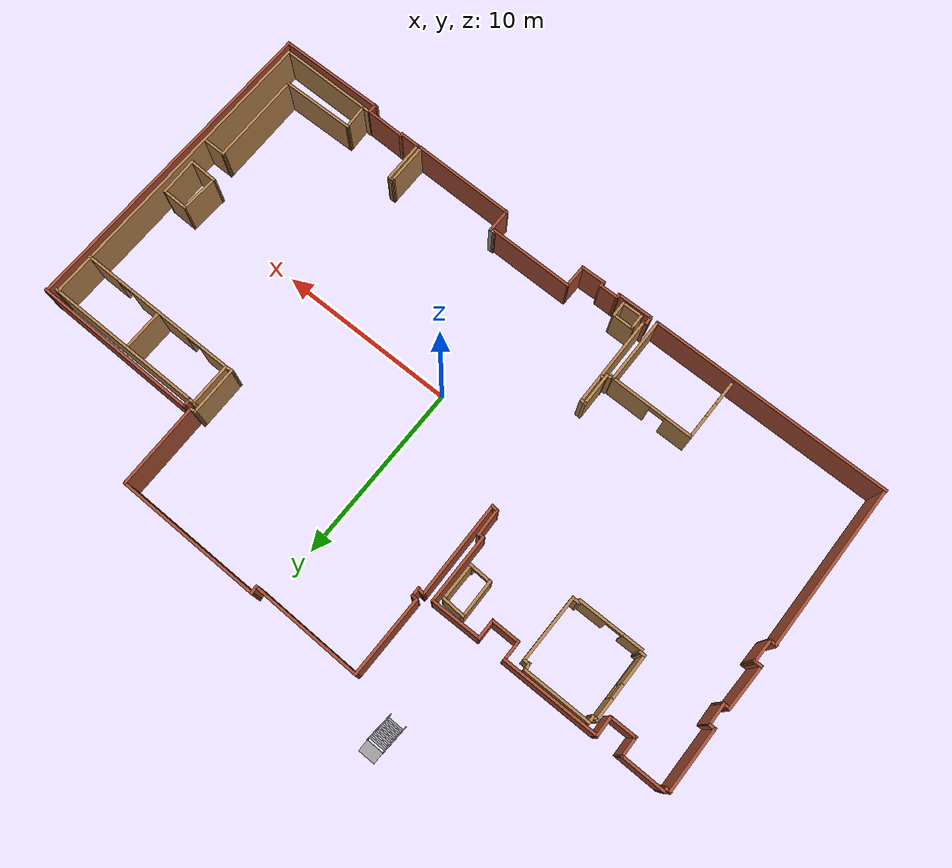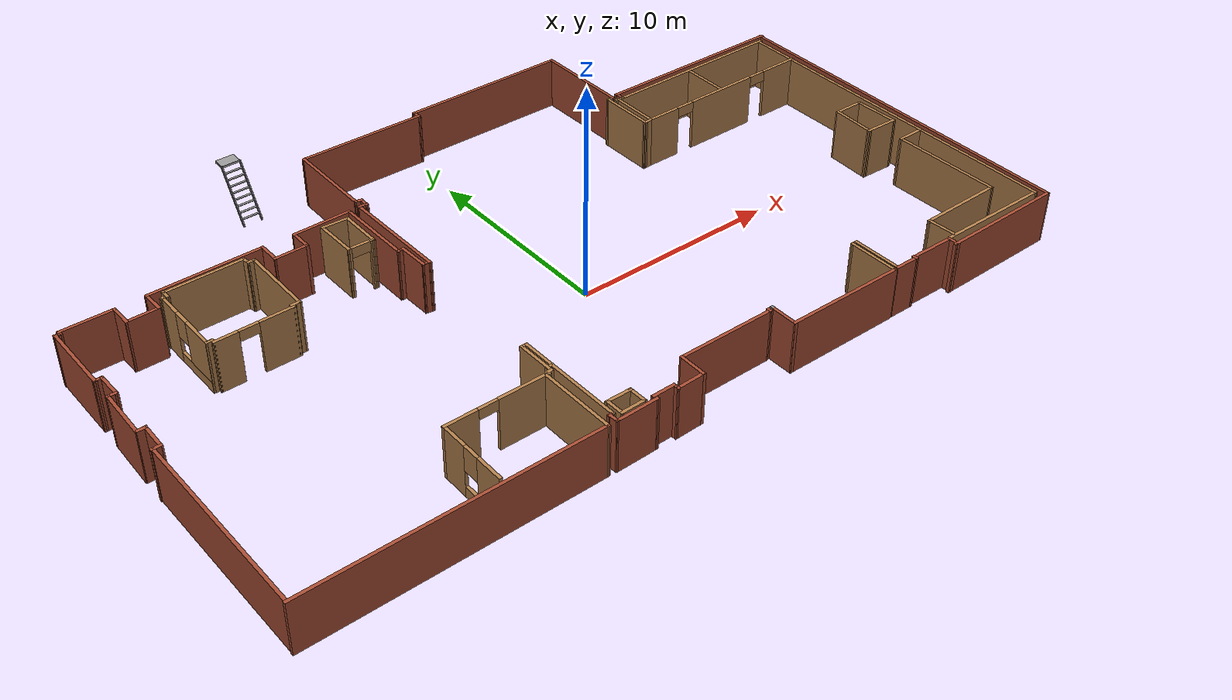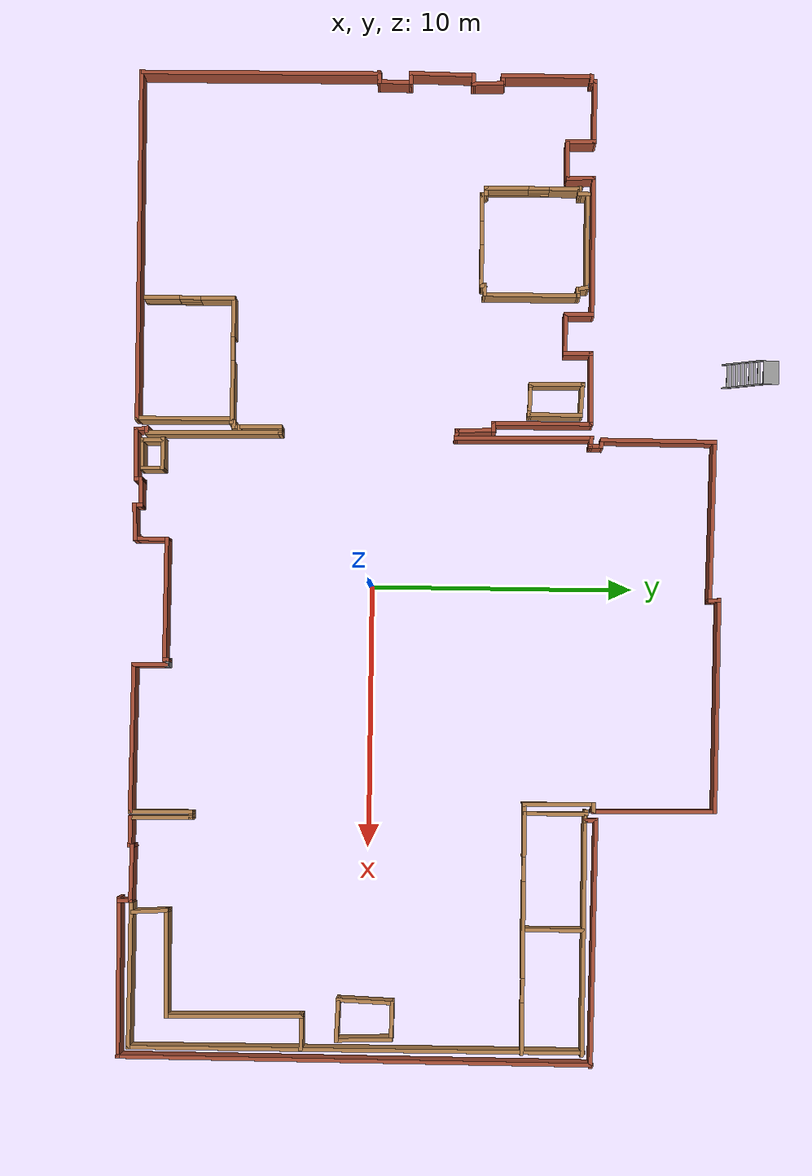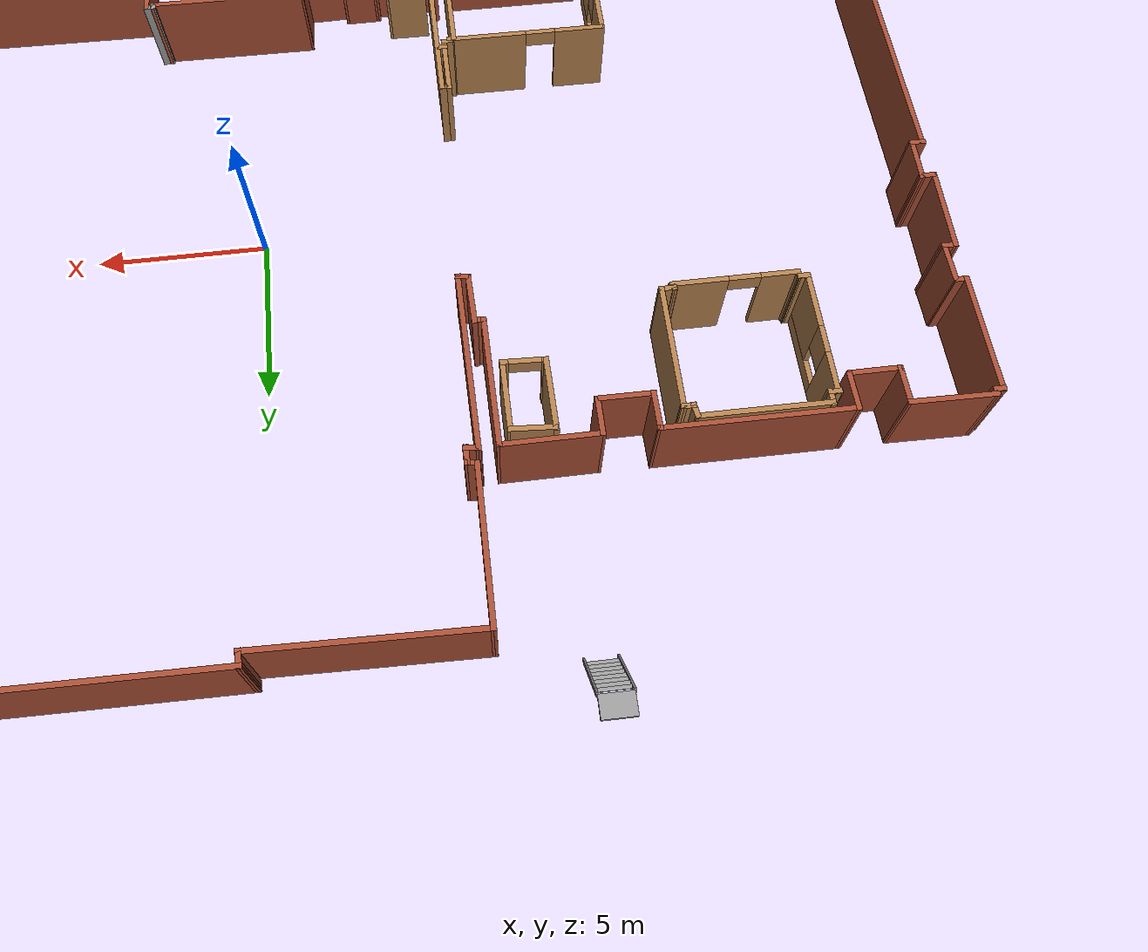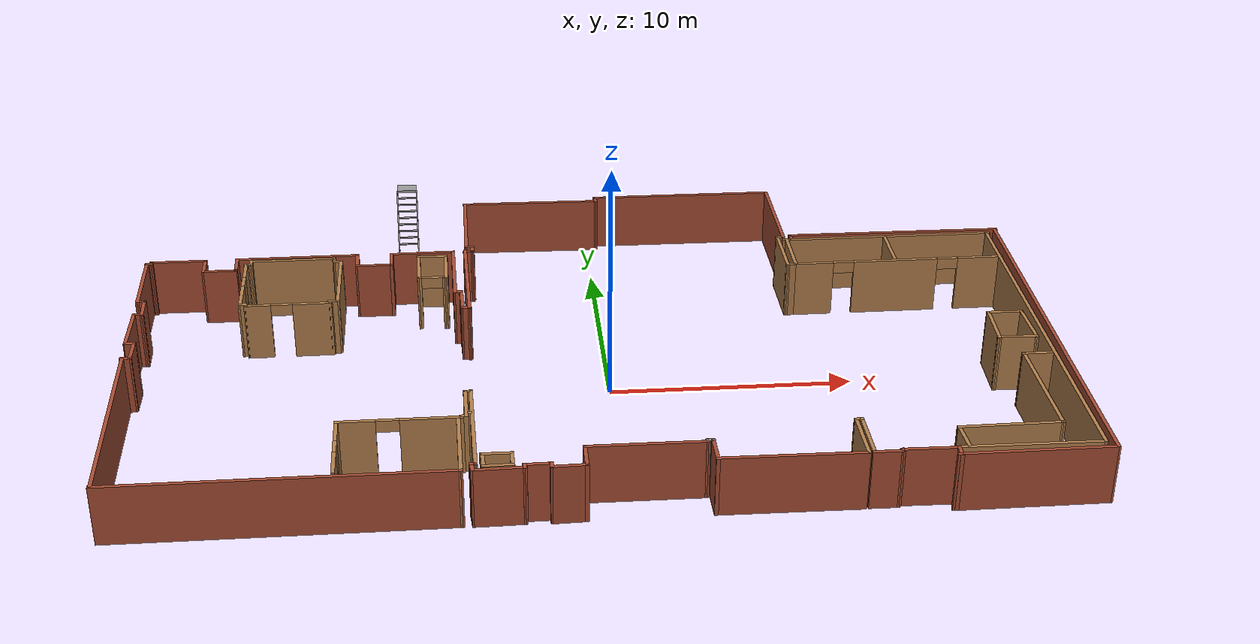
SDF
<sdf version="1.7">
 <world name="empty_world">
  <physics type="ode">
   <max_step_size>0.01</max_step_size>
   <real_time_factor>1</real_time_factor>
   <real_time_update_rate>1000</real_time_update_rate>
  </physics>
  <light name="sun" type="directional">
   <pose>0 0 10 0 -0 0</pose>
   <diffuse>0.8 0.8 0.8 1</diffuse>
   <specular>0.2 0.2 0.2 1</specular>
   <attenuation>
    <range>1000</range>
    <constant>0.9</constant>
    <linear>0.01</linear>
    <quadratic>0.001</quadratic>
   </attenuation>
   <direction>-0.5 0.1 -0.9</direction>
   <spot><inner_angle>0</inner_angle><outer_angle>0</outer_angle><falloff>0</falloff></spot>
  </light>
  <gravity>0 0 -9.8</gravity>
  <magnetic_field>6e-06 2.3e-05 -4.2e-05</magnetic_field>
  <atmosphere type="adiabatic"/>
  <scene><ambient>0.4 0.4 0.4 1</ambient><background>0.7 0.7 0.7 1</background><shadows>1</shadows></scene>
  <audio><device>default</device></audio>
  <spherical_coordinates>
   <surface_model>EARTH_WGS84</surface_model>
   <latitude_deg>0</latitude_deg>
   <longitude_deg>0</longitude_deg>
   <elevation>0</elevation>
   <heading_deg>0</heading_deg>
  </spherical_coordinates>
  <model name="my_floor">
   <pose>-0.708738 1.92561 0 0 -0 0</pose>
   <link name="Wall_100">
    <collision name="Wall_100_Collision">
     <geometry><box><size>1.2289 0.15 2.5</size></box></geometry>
     <pose>0 0 1.25 0 -0 0</pose>
    </collision>
    <visual name="Wall_100_Visual">
     <pose>0 0 1.25 0 -0 0</pose>
     <geometry><box><size>1.2289 0.15 2.5</size></box></geometry>
     <material>
      <script><uri>file://media/materials/scripts/gazebo.material</uri><name>Gazebo/Wood</name></script>
      <ambient>1 1 1 1</ambient>
     </material>
     <meta><layer>0</layer></meta>
    </visual>
    <pose>-4.18649 -10.7209 0 0 -0 -3.12644</pose>
   </link>
   <link name="Wall_101">
    <collision name="Wall_101_Collision">
     <geometry><box><size>0.895451 0.15 2.5</size></box></geometry>
     <pose>0 0 1.25 0 -0 0</pose>
    </collision>
    <visual name="Wall_101_Visual">
     <pose>0 0 1.25 0 -0 0</pose>
     <geometry><box><size>0.895451 0.15 2.5</size></box></geometry>
     <material>
      <script><uri>file://media/materials/scripts/gazebo.material</uri><name>Gazebo/Wood</name></script>
      <ambient>1 1 1 1</ambient>
     </material>
     <meta><layer>0</layer></meta>
    </visual>
    <pose>-4.73242 -10.3564 0 0 -0 1.58834</pose>
   </link>
   <link name="Wall_103">
    <collision name="Wall_103_Collision">
     <geometry><box><size>5.21545 0.15 2.5</size></box></geometry>
     <pose>0 0 1.25 0 -0 0</pose>
    </collision>
    <visual name="Wall_103_Visual">
     <pose>0 0 1.25 0 -0 0</pose>
     <geometry><box><size>5.21545 0.15 2.5</size></box></geometry>
     <material>
      <script><uri>file://media/materials/scripts/gazebo.material</uri><name>Gazebo/Wood</name></script>
      <ambient>1 1 1 1</ambient>
     </material>
     <meta><layer>0</layer></meta>
    </visual>
    <pose>-5.03494 -8.01189 0 0 -0 1.58124</pose>
   </link>
   <link name="Wall_105">
    <collision name="Wall_105_Collision">
     <geometry><box><size>0.334792 0.15 2.5</size></box></geometry>
     <pose>0 0 1.25 0 -0 0</pose>
    </collision>
    <visual name="Wall_105_Visual">
     <pose>0 0 1.25 0 -0 0</pose>
     <geometry><box><size>0.334792 0.15 2.5</size></box></geometry>
     <material>
      <script><uri>file://media/materials/scripts/gazebo.material</uri><name>Gazebo/Wood</name></script>
      <ambient>1 1 1 1</ambient>
     </material>
     <meta><layer>0</layer></meta>
    </visual>
    <pose>-5.15008 -5.4634 0 0 -0 -3.12621</pose>
   </link>
   <link name="Wall_107">
    <collision name="Wall_107_Collision">
     <geometry><box><size>1.93127 0.15 2.5</size></box></geometry>
     <pose>0 0 1.25 0 -0 0</pose>
    </collision>
    <visual name="Wall_107_Visual">
     <pose>0 0 1.25 0 -0 0</pose>
     <geometry><box><size>1.93127 0.15 2.5</size></box></geometry>
     <material>
      <script><uri>file://media/materials/scripts/gazebo.material</uri><name>Gazebo/Wood</name></script>
      <ambient>1 1 1 1</ambient>
     </material>
     <meta><layer>0</layer></meta>
    </visual>
    <pose>-5.26553 -6.34786 0 0 -0 -1.56109</pose>
   </link>
   <link name="Wall_109">
    <collision name="Wall_109_Collision">
     <geometry><box><size>0.315671 0.15 2.5</size></box></geometry>
     <pose>0 0 1.25 0 -0 0</pose>
    </collision>
    <visual name="Wall_109_Visual">
     <pose>0 0 1.25 0 -0 0</pose>
     <geometry><box><size>0.315671 0.15 2.5</size></box></geometry>
     <material>
      <script><uri>file://media/materials/scripts/gazebo.material</uri><name>Gazebo/Wood</name></script>
      <ambient>1 1 1 1</ambient>
     </material>
     <meta><layer>0</layer></meta>
    </visual>
    <pose>-5.1931 -7.03195 0 0 -0 3.12224</pose>
   </link>
   <link name="Wall_11">
    <collision name="Wall_11_Collision">
     <geometry><box><size>1.12811 0.15 2.5</size></box></geometry>
     <pose>0 0 1.25 0 -0 0</pose>
    </collision>
    <visual name="Wall_11_Visual">
     <pose>0 0 1.25 0 -0 0</pose>
     <geometry><box><size>1.12811 0.15 2.5</size></box></geometry>
     <material>
      <script><uri>file://media/materials/scripts/gazebo.material</uri><name>Gazebo/Bricks</name></script>
      <ambient>1 1 1 1</ambient>
     </material>
     <meta><layer>0</layer></meta>
    </visual>
    <pose>-14.952 5.89159 0 0 -0 1.59432</pose>
   </link>
   <link name="Wall_111">
    <collision name="Wall_111_Collision">
     <geometry><box><size>0.259007 0.15 2.5</size></box></geometry>
     <pose>0 0 1.25 0 -0 0</pose>
    </collision>
    <visual name="Wall_111_Visual">
     <pose>0 0 1.25 0 -0 0</pose>
     <geometry><box><size>0.259007 0.15 2.5</size></box></geometry>
     <material>
      <script><uri>file://media/materials/scripts/gazebo.material</uri><name>Gazebo/Wood</name></script>
      <ambient>1 1 1 1</ambient>
     </material>
     <meta><layer>0</layer></meta>
    </visual>
    <pose>-5.4928 -7.3408 0 0 -0 -3.13179</pose>
   </link>
   <link name="Wall_113">
    <collision name="Wall_113_Collision">
     <geometry><box><size>0.352916 0.15 2.5</size></box></geometry>
     <pose>0 0 1.25 0 -0 0</pose>
    </collision>
    <visual name="Wall_113_Visual">
     <pose>0 0 1.25 0 -0 0</pose>
     <geometry><box><size>0.352916 0.15 2.5</size></box></geometry>
     <material>
      <script><uri>file://media/materials/scripts/gazebo.material</uri><name>Gazebo/Wood</name></script>
      <ambient>1 1 1 1</ambient>
     </material>
     <meta><layer>0</layer></meta>
    </visual>
    <pose>-5.36071 -7.24954 0 0 -0 -3.09324</pose>
   </link>
   <link name="Wall_115">
    <collision name="Wall_115_Collision">
     <geometry><box><size>3.77375 0.15 2.5</size></box></geometry>
     <pose>0 0 1.25 0 -0 0</pose>
    </collision>
    <visual name="Wall_115_Visual">
     <pose>0 0 1.25 0 -0 0</pose>
     <geometry><box><size>3.77375 0.15 2.5</size></box></geometry>
     <material>
      <script><uri>file://media/materials/scripts/gazebo.material</uri><name>Gazebo/Wood</name></script>
      <ambient>1 1 1 1</ambient>
     </material>
     <meta><layer>0</layer></meta>
    </visual>
    <pose>-5.56089 -9.12692 0 0 -0 -1.5635</pose>
   </link>
   <link name="Wall_116">
    <collision name="Wall_116_Collision">
     <geometry><box><size>13.4279 0.15 2.5</size></box></geometry>
     <pose>0 0 1.25 0 -0 0</pose>
    </collision>
    <visual name="Wall_116_Visual">
     <pose>0 0 1.25 0 -0 0</pose>
     <geometry><box><size>13.4279 0.15 2.5</size></box></geometry>
     <material>
      <script><uri>file://media/materials/scripts/gazebo.material</uri><name>Gazebo/Bricks</name></script>
      <ambient>1 1 1 1</ambient>
     </material>
     <meta><layer>0</layer></meta>
    </visual>
    <pose>-12.1866 -10.952 0 0 -0 -3.1396</pose>
   </link>
   <link name="Wall_118">
    <collision name="Wall_118_Collision">
     <geometry><box><size>9.16762 0.15 2.5</size></box></geometry>
     <pose>0 0 1.25 0 -0 0</pose>
    </collision>
    <visual name="Wall_118_Visual">
     <pose>0 0 1.25 0 -0 0</pose>
     <geometry><box><size>9.16762 0.15 2.5</size></box></geometry>
     <material>
      <script><uri>file://media/materials/scripts/gazebo.material</uri><name>Gazebo/Bricks</name></script>
      <ambient>1 1 1 1</ambient>
     </material>
     <meta><layer>0</layer></meta>
    </visual>
    <pose>-18.8288 -6.37885 0 0 -0 1.5767</pose>
   </link>
   <link name="Wall_12">
    <collision name="Wall_12_Collision">
     <geometry><box><size>5.3825 0.15 2.5</size></box></geometry>
     <pose>0 0 1.25 0 -0 0</pose>
    </collision>
    <visual name="Wall_12_Visual">
     <pose>0 0 1.25 0 -0 0</pose>
     <geometry><box><size>5.3825 0.15 2.5</size></box></geometry>
     <material>
      <script><uri>file://media/materials/scripts/gazebo.material</uri><name>Gazebo/Bricks</name></script>
      <ambient>1 1 1 1</ambient>
     </material>
     <meta><layer>0</layer></meta>
    </visual>
    <pose>-12.3472 6.38034 0 0 -0 0</pose>
   </link>
   <link name="Wall_120">
    <collision name="Wall_120_Collision">
     <geometry><box><size>0.485333 0.15 2.5</size></box></geometry>
     <pose>0 0 1.25 0 -0 0</pose>
    </collision>
    <visual name="Wall_120_Visual">
     <pose>0 0 1.25 0 -0 0</pose>
     <geometry><box><size>0.485333 0.15 2.5</size></box></geometry>
     <material>
      <script><uri>file://media/materials/scripts/gazebo.material</uri><name>Gazebo/Bricks</name></script>
      <ambient>1 1 1 1</ambient>
     </material>
     <meta><layer>0</layer></meta>
    </visual>
    <pose>-18.7212 -1.85978 0 0 -0 0</pose>
   </link>
   <link name="Wall_121">
    <collision name="Wall_121_Collision">
     <geometry><box><size>1.35342 0.15 2.5</size></box></geometry>
     <pose>0 0 1.25 0 -0 0</pose>
    </collision>
    <visual name="Wall_121_Visual">
     <pose>0 0 1.25 0 -0 0</pose>
     <geometry><box><size>1.35342 0.15 2.5</size></box></geometry>
     <material>
      <script><uri>file://media/materials/scripts/gazebo.material</uri><name>Gazebo/Bricks</name></script>
      <ambient>1 1 1 1</ambient>
     </material>
     <meta><layer>0</layer></meta>
    </visual>
    <pose>-18.5436 -1.25815 0 0 -0 1.5544</pose>
   </link>
   <link name="Wall_122">
    <collision name="Wall_122_Collision">
     <geometry><box><size>0.472451 0.15 2.5</size></box></geometry>
     <pose>0 0 1.25 0 -0 0</pose>
    </collision>
    <visual name="Wall_122_Visual">
     <pose>0 0 1.25 0 -0 0</pose>
     <geometry><box><size>0.472451 0.15 2.5</size></box></geometry>
     <material>
      <script><uri>file://media/materials/scripts/gazebo.material</uri><name>Gazebo/Bricks</name></script>
      <ambient>1 1 1 1</ambient>
     </material>
     <meta><layer>0</layer></meta>
    </visual>
    <pose>-18.6949 -0.6631 0 0 -0 -3.1008</pose>
   </link>
   <link name="Wall_124">
    <collision name="Wall_124_Collision">
     <geometry><box><size>2.54244 0.15 2.5</size></box></geometry>
     <pose>0 0 1.25 0 -0 0</pose>
    </collision>
    <visual name="Wall_124_Visual">
     <pose>0 0 1.25 0 -0 0</pose>
     <geometry><box><size>2.54244 0.15 2.5</size></box></geometry>
     <material>
      <script><uri>file://media/materials/scripts/gazebo.material</uri><name>Gazebo/Bricks</name></script>
      <ambient>1 1 1 1</ambient>
     </material>
     <meta><layer>0</layer></meta>
    </visual>
    <pose>-18.8667 0.544978 0 0 -0 1.55157</pose>
   </link>
   <link name="Wall_125">
    <collision name="Wall_125_Collision">
     <geometry><box><size>0.472205 0.15 2.5</size></box></geometry>
     <pose>0 0 1.25 0 -0 0</pose>
    </collision>
    <visual name="Wall_125_Visual">
     <pose>0 0 1.25 0 -0 0</pose>
     <geometry><box><size>0.472205 0.15 2.5</size></box></geometry>
     <material>
      <script><uri>file://media/materials/scripts/gazebo.material</uri><name>Gazebo/Bricks</name></script>
      <ambient>1 1 1 1</ambient>
     </material>
     <meta><layer>0</layer></meta>
    </visual>
    <pose>-18.6827 1.73523 0 0 -0 -0.035699</pose>
   </link>
   <link name="Wall_126">
    <collision name="Wall_126_Collision">
     <geometry><box><size>1.24274 0.15 2.5</size></box></geometry>
     <pose>0 0 1.25 0 -0 0</pose>
    </collision>
    <visual name="Wall_126_Visual">
     <pose>0 0 1.25 0 -0 0</pose>
     <geometry><box><size>1.24274 0.15 2.5</size></box></geometry>
     <material>
      <script><uri>file://media/materials/scripts/gazebo.material</uri><name>Gazebo/Bricks</name></script>
      <ambient>1 1 1 1</ambient>
     </material>
     <meta><layer>0</layer></meta>
    </visual>
    <pose>-18.5332 2.27573 0 0 -0 1.59185</pose>
   </link>
   <link name="Wall_128">
    <collision name="Wall_128_Collision">
     <geometry><box><size>2.23103 0.15 2.5</size></box></geometry>
     <pose>0 0 1.25 0 -0 0</pose>
    </collision>
    <visual name="Wall_128_Visual">
     <pose>0 0 1.25 0 -0 0</pose>
     <geometry><box><size>2.23103 0.15 2.5</size></box></geometry>
     <material>
      <script><uri>file://media/materials/scripts/gazebo.material</uri><name>Gazebo/Wood</name></script>
      <ambient>1 1 1 1</ambient>
     </material>
     <meta><layer>0</layer></meta>
    </visual>
    <pose>17.993 -1.97873 0 0 -0 -1.54139</pose>
   </link>
   <link name="Wall_129">
    <collision name="Wall_129_Collision">
     <geometry><box><size>1.68074 0.15 2.5</size></box></geometry>
     <pose>0 0 1.25 0 -0 0</pose>
    </collision>
    <visual name="Wall_129_Visual">
     <pose>0 0 1.25 0 -0 0</pose>
     <geometry><box><size>1.68074 0.15 2.5</size></box></geometry>
     <material>
      <script><uri>file://media/materials/scripts/gazebo.material</uri><name>Gazebo/Wood</name></script>
      <ambient>1 1 1 1</ambient>
     </material>
     <meta><layer>0</layer></meta>
    </visual>
    <pose>17.2589 -2.98821 0 0 -0 3.10161</pose>
   </link>
   <link name="Wall_13">
    <collision name="Wall_13_Collision">
     <geometry><box><size>1.16206 0.15 2.5</size></box></geometry>
     <pose>0 0 1.25 0 -0 0</pose>
    </collision>
    <visual name="Wall_13_Visual">
     <pose>0 0 1.25 0 -0 0</pose>
     <geometry><box><size>1.16206 0.15 2.5</size></box></geometry>
     <material>
      <script><uri>file://media/materials/scripts/gazebo.material</uri><name>Gazebo/Bricks</name></script>
      <ambient>1 1 1 1</ambient>
     </material>
     <meta><layer>0</layer></meta>
    </visual>
    <pose>-9.72525 5.87434 0 0 -0 -1.55943</pose>
   </link>
   <link name="Wall_130">
    <collision name="Wall_130_Collision">
     <geometry><box><size>2.2016 0.15 2.5</size></box></geometry>
     <pose>0 0 1.25 0 -0 0</pose>
    </collision>
    <visual name="Wall_130_Visual">
     <pose>0 0 1.25 0 -0 0</pose>
     <geometry><box><size>2.2016 0.15 2.5</size></box></geometry>
     <material>
      <script><uri>file://media/materials/scripts/gazebo.material</uri><name>Gazebo/Wood</name></script>
      <ambient>1 1 1 1</ambient>
     </material>
     <meta><layer>0</layer></meta>
    </visual>
    <pose>16.54 -1.93285 0 0 -0 1.52605</pose>
   </link>
   <link name="Wall_131">
    <collision name="Wall_131_Collision">
     <geometry><box><size>1.5269 0.15 2.5</size></box></geometry>
     <pose>0 0 1.25 0 -0 0</pose>
    </collision>
    <visual name="Wall_131_Visual">
     <pose>0 0 1.25 0 -0 0</pose>
     <geometry><box><size>1.5269 0.15 2.5</size></box></geometry>
     <material>
      <script><uri>file://media/materials/scripts/gazebo.material</uri><name>Gazebo/Wood</name></script>
      <ambient>1 1 1 1</ambient>
     </material>
     <meta><layer>0</layer></meta>
    </visual>
    <pose>17.2742 -0.923369 0 0 -0 -0.022219</pose>
   </link>
   <link name="Wall_133">
    <collision name="Wall_133_Collision">
     <geometry><box><size>1.39905 0.15 2.5</size></box></geometry>
     <pose>0 0 1.25 0 -0 0</pose>
    </collision>
    <visual name="Wall_133_Visual">
     <pose>0 0 1.25 0 -0 0</pose>
     <geometry><box><size>1.39905 0.15 2.5</size></box></geometry>
     <material>
      <script><uri>file://media/materials/scripts/gazebo.material</uri><name>Gazebo/Wood</name></script>
      <ambient>1 1 1 1</ambient>
     </material>
     <meta><layer>0</layer></meta>
    </visual>
    <pose>17.7418 -4.35062 0 0 -0 3.14159</pose>
   </link>
   <link name="Wall_134">
    <collision name="Wall_134_Collision">
     <geometry><box><size>5.28546 0.15 2.5</size></box></geometry>
     <pose>0 0 1.25 0 -0 0</pose>
    </collision>
    <visual name="Wall_134_Visual">
     <pose>0 0 1.25 0 -0 0</pose>
     <geometry><box><size>5.28546 0.15 2.5</size></box></geometry>
     <material>
      <script><uri>file://media/materials/scripts/gazebo.material</uri><name>Gazebo/Wood</name></script>
      <ambient>1 1 1 1</ambient>
     </material>
     <meta><layer>0</layer></meta>
    </visual>
    <pose>17.1519 -6.91811 0 0 -0 -1.55728</pose>
   </link>
   <link name="Wall_135">
    <collision name="Wall_135_Collision">
     <geometry><box><size>4.15186 0.15 2.5</size></box></geometry>
     <pose>0 0 1.25 0 -0 0</pose>
    </collision>
    <visual name="Wall_135_Visual">
     <pose>0 0 1.25 0 -0 0</pose>
     <geometry><box><size>4.15186 0.15 2.5</size></box></geometry>
     <material>
      <script><uri>file://media/materials/scripts/gazebo.material</uri><name>Gazebo/Wood</name></script>
      <ambient>1 1 1 1</ambient>
     </material>
     <meta><layer>0</layer></meta>
    </visual>
    <pose>15.1858 -9.50874 0 0 -0 -3.13003</pose>
   </link>
   <link name="Wall_136">
    <collision name="Wall_136_Collision">
     <geometry><box><size>1.42407 0.15 2.5</size></box></geometry>
     <pose>0 0 1.25 0 -0 0</pose>
    </collision>
    <visual name="Wall_136_Visual">
     <pose>0 0 1.25 0 -0 0</pose>
     <geometry><box><size>1.42407 0.15 2.5</size></box></geometry>
     <material>
      <script><uri>file://media/materials/scripts/gazebo.material</uri><name>Gazebo/Wood</name></script>
      <ambient>1 1 1 1</ambient>
     </material>
     <meta><layer>0</layer></meta>
    </visual>
    <pose>13.2197 -10.168 0 0 -0 -1.51631</pose>
   </link>
   <link name="Wall_139">
    <pose>-7.87411 -7.31509 0 0 -0 3.14159</pose>
    <visual name="Wall_139_Visual_0">
     <pose>-1.22688 0 1.25 0 -0 0</pose>
     <geometry><box><size>2.29625 0.15 2.5</size></box></geometry>
     <material>
      <script><uri>file://media/materials/scripts/gazebo.material</uri><name>Gazebo/Wood</name></script>
      <ambient>1 1 1 1</ambient>
     </material>
     <meta><layer>0</layer></meta>
    </visual>
    <collision name="Wall_139_Collision_0">
     <geometry><box><size>2.29625 0.15 2.5</size></box></geometry>
     <pose>-1.22688 0 1.25 0 -0 0</pose>
    </collision>
    <visual name="Wall_139_Visual_1">
     <pose>1.59812 0 1.25 0 -0 0</pose>
     <geometry><box><size>1.55375 0.15 2.5</size></box></geometry>
     <material>
      <script><uri>file://media/materials/scripts/gazebo.material</uri><name>Gazebo/Wood</name></script>
      <ambient>1 1 1 1</ambient>
     </material>
     <meta><layer>0</layer></meta>
    </visual>
    <collision name="Wall_139_Collision_1">
     <geometry><box><size>1.55375 0.15 2.5</size></box></geometry>
     <pose>1.59812 0 1.25 0 -0 0</pose>
    </collision>
    <visual name="Wall_139_Visual_2">
     <pose>0.371246 0 2.25 0 -0 0</pose>
     <geometry><box><size>0.9 0.15 0.5</size></box></geometry>
     <material>
      <script><uri>file://media/materials/scripts/gazebo.material</uri><name>Gazebo/Wood</name></script>
      <ambient>1 1 1 1</ambient>
     </material>
     <meta><layer>0</layer></meta>
    </visual>
    <collision name="Wall_139_Collision_2">
     <geometry><box><size>0.9 0.15 0.5</size></box></geometry>
     <pose>0.371246 0 2.25 0 -0 0</pose>
    </collision>
   </link>
   <link name="Wall_14">
    <collision name="Wall_14_Collision">
     <geometry><box><size>1.6335 0.15 2.5</size></box></geometry>
     <pose>0 0 1.25 0 -0 0</pose>
    </collision>
    <visual name="Wall_14_Visual">
     <pose>0 0 1.25 0 -0 0</pose>
     <geometry><box><size>1.6335 0.15 2.5</size></box></geometry>
     <material>
      <script><uri>file://media/materials/scripts/gazebo.material</uri><name>Gazebo/Bricks</name></script>
      <ambient>1 1 1 1</ambient>
     </material>
     <meta><layer>0</layer></meta>
    </visual>
    <pose>-8.97775 5.36834 0 0 -0 0</pose>
   </link>
   <link name="Wall_140">
    <pose>-10.1741 -8.99009 0 0 -0 -1.5708</pose>
    <visual name="Wall_140_Visual_0">
     <pose>-1.07557 0 1.25 0 -0 0</pose>
     <geometry><box><size>1.34886 0.15 2.5</size></box></geometry>
     <material>
      <script><uri>file://media/materials/scripts/gazebo.material</uri><name>Gazebo/Wood</name></script>
      <ambient>1 1 1 1</ambient>
     </material>
     <meta><layer>0</layer></meta>
    </visual>
    <collision name="Wall_140_Collision_0">
     <geometry><box><size>1.34886 0.15 2.5</size></box></geometry>
     <pose>-1.07557 0 1.25 0 -0 0</pose>
    </collision>
    <visual name="Wall_140_Visual_1">
     <pose>0.674431 0 0.25 0 -0 0</pose>
     <geometry><box><size>2.15114 0.15 0.5</size></box></geometry>
     <material>
      <script><uri>file://media/materials/scripts/gazebo.material</uri><name>Gazebo/Wood</name></script>
      <ambient>1 1 1 1</ambient>
     </material>
     <meta><layer>0</layer></meta>
    </visual>
    <collision name="Wall_140_Collision_1">
     <geometry><box><size>2.15114 0.15 0.5</size></box></geometry>
     <pose>0.674431 0 0.25 0 -0 0</pose>
    </collision>
    <visual name="Wall_140_Visual_2">
     <pose>1.07443 0 1.5 0 -0 0</pose>
     <geometry><box><size>1.35114 0.15 2</size></box></geometry>
     <material>
      <script><uri>file://media/materials/scripts/gazebo.material</uri><name>Gazebo/Wood</name></script>
      <ambient>1 1 1 1</ambient>
     </material>
     <meta><layer>0</layer></meta>
    </visual>
    <collision name="Wall_140_Collision_2">
     <geometry><box><size>1.35114 0.15 2</size></box></geometry>
     <pose>1.07443 0 1.5 0 -0 0</pose>
    </collision>
    <visual name="Wall_140_Visual_3">
     <pose>-0.001139 0 1.9 0 -0 0</pose>
     <geometry><box><size>0.8 0.15 1.2</size></box></geometry>
     <material>
      <script><uri>file://media/materials/scripts/gazebo.material</uri><name>Gazebo/Wood</name></script>
      <ambient>1 1 1 1</ambient>
     </material>
     <meta><layer>0</layer></meta>
    </visual>
    <collision name="Wall_140_Collision_3">
     <geometry><box><size>0.8 0.15 1.2</size></box></geometry>
     <pose>-0.001139 0 1.9 0 -0 0</pose>
    </collision>
   </link>
   <link name="Wall_142">
    <pose>13.8818 4.03162 0 0 -0 0</pose>
    <visual name="Wall_142_Visual_0">
     <pose>-3.75662 0 1.25 0 -0 0</pose>
     <geometry><box><size>1.73677 0.15 2.5</size></box></geometry>
     <material>
      <script><uri>file://media/materials/scripts/gazebo.material</uri><name>Gazebo/Wood</name></script>
      <ambient>1 1 1 1</ambient>
     </material>
     <meta><layer>0</layer></meta>
    </visual>
    <collision name="Wall_142_Collision_0">
     <geometry><box><size>1.73677 0.15 2.5</size></box></geometry>
     <pose>-3.75662 0 1.25 0 -0 0</pose>
    </collision>
    <visual name="Wall_142_Visual_1">
     <pose>-0.137622 0 1.25 0 -0 0</pose>
     <geometry><box><size>3.70121 0.15 2.5</size></box></geometry>
     <material>
      <script><uri>file://media/materials/scripts/gazebo.material</uri><name>Gazebo/Wood</name></script>
      <ambient>1 1 1 1</ambient>
     </material>
     <meta><layer>0</layer></meta>
    </visual>
    <collision name="Wall_142_Collision_1">
     <geometry><box><size>3.70121 0.15 2.5</size></box></geometry>
     <pose>-0.137622 0 1.25 0 -0 0</pose>
    </collision>
    <visual name="Wall_142_Visual_2">
     <pose>3.61899 0 1.25 0 -0 0</pose>
     <geometry><box><size>2.01201 0.15 2.5</size></box></geometry>
     <material>
      <script><uri>file://media/materials/scripts/gazebo.material</uri><name>Gazebo/Wood</name></script>
      <ambient>1 1 1 1</ambient>
     </material>
     <meta><layer>0</layer></meta>
    </visual>
    <collision name="Wall_142_Collision_2">
     <geometry><box><size>2.01201 0.15 2.5</size></box></geometry>
     <pose>3.61899 0 1.25 0 -0 0</pose>
    </collision>
    <visual name="Wall_142_Visual_3">
     <pose>-2.43823 0 2.25 0 -0 0</pose>
     <geometry><box><size>0.9 0.15 0.5</size></box></geometry>
     <material>
      <script><uri>file://media/materials/scripts/gazebo.material</uri><name>Gazebo/Wood</name></script>
      <ambient>1 1 1 1</ambient>
     </material>
     <meta><layer>0</layer></meta>
    </visual>
    <collision name="Wall_142_Collision_3">
     <geometry><box><size>0.9 0.15 0.5</size></box></geometry>
     <pose>-2.43823 0 2.25 0 -0 0</pose>
    </collision>
    <visual name="Wall_142_Visual_4">
     <pose>2.16298 0 2.25 0 -0 0</pose>
     <geometry><box><size>0.9 0.15 0.5</size></box></geometry>
     <material>
      <script><uri>file://media/materials/scripts/gazebo.material</uri><name>Gazebo/Wood</name></script>
      <ambient>1 1 1 1</ambient>
     </material>
     <meta><layer>0</layer></meta>
    </visual>
    <collision name="Wall_142_Collision_4">
     <geometry><box><size>0.9 0.15 0.5</size></box></geometry>
     <pose>2.16298 0 2.25 0 -0 0</pose>
    </collision>
   </link>
   <link name="Wall_144">
    <collision name="Wall_144_Collision">
     <geometry><box><size>2.25 0.15 2.5</size></box></geometry>
     <pose>0 0 1.25 0 -0 0</pose>
    </collision>
    <visual name="Wall_144_Visual">
     <pose>0 0 1.25 0 -0 0</pose>
     <geometry><box><size>2.25 0.15 2.5</size></box></geometry>
     <material>
      <script><uri>file://media/materials/scripts/gazebo.material</uri><name>Gazebo/Wood</name></script>
      <ambient>1 1 1 1</ambient>
     </material>
     <meta><layer>0</layer></meta>
    </visual>
    <pose>13.7442 5.22429 0 0 -0 1.5708</pose>
   </link>
   <link name="Wall_15">
    <collision name="Wall_15_Collision">
     <geometry><box><size>1.13907 0.15 2.5</size></box></geometry>
     <pose>0 0 1.25 0 -0 0</pose>
    </collision>
    <visual name="Wall_15_Visual">
     <pose>0 0 1.25 0 -0 0</pose>
     <geometry><box><size>1.13907 0.15 2.5</size></box></geometry>
     <material>
      <script><uri>file://media/materials/scripts/gazebo.material</uri><name>Gazebo/Bricks</name></script>
      <ambient>1 1 1 1</ambient>
     </material>
     <meta><layer>0</layer></meta>
    </visual>
    <pose>-8.236 5.86284 0 0 -0 1.5708</pose>
   </link>
   <link name="Wall_16">
    <collision name="Wall_16_Collision">
     <geometry><box><size>2.8411 0.15 2.5</size></box></geometry>
     <pose>0 0 1.25 0 -0 0</pose>
    </collision>
    <visual name="Wall_16_Visual">
     <pose>0 0 1.25 0 -0 0</pose>
     <geometry><box><size>2.8411 0.15 2.5</size></box></geometry>
     <material>
      <script><uri>file://media/materials/scripts/gazebo.material</uri><name>Gazebo/Bricks</name></script>
      <ambient>1 1 1 1</ambient>
     </material>
     <meta><layer>0</layer></meta>
    </visual>
    <pose>-6.8905 6.36884 0 0 -0 0.008547</pose>
   </link>
   <link name="Wall_17">
    <collision name="Wall_17_Collision">
     <geometry><box><size>3.86466 0.15 2.5</size></box></geometry>
     <pose>0 0 1.25 0 -0 0</pose>
    </collision>
    <visual name="Wall_17_Visual">
     <pose>0 0 1.25 0 -0 0</pose>
     <geometry><box><size>3.86466 0.15 2.5</size></box></geometry>
     <material>
      <script><uri>file://media/materials/scripts/gazebo.material</uri><name>Gazebo/Bricks</name></script>
      <ambient>1 1 1 1</ambient>
     </material>
     <meta><layer>0</layer></meta>
    </visual>
    <pose>-5.52775 4.52309 0 0 -0 -1.56151</pose>
   </link>
   <link name="Wall_18">
    <collision name="Wall_18_Collision">
     <geometry><box><size>0.403 0.15 2.5</size></box></geometry>
     <pose>0 0 1.25 0 -0 0</pose>
    </collision>
    <visual name="Wall_18_Visual">
     <pose>0 0 1.25 0 -0 0</pose>
     <geometry><box><size>0.403 0.15 2.5</size></box></geometry>
     <material>
      <script><uri>file://media/materials/scripts/gazebo.material</uri><name>Gazebo/Bricks</name></script>
      <ambient>1 1 1 1</ambient>
     </material>
     <meta><layer>0</layer></meta>
    </visual>
    <pose>-5.384 2.66584 0 0 -0 0</pose>
   </link>
   <link name="Wall_2">
    <collision name="Wall_2_Collision">
     <geometry><box><size>3.56024 0.15 2.5</size></box></geometry>
     <pose>0 0 1.25 0 -0 0</pose>
    </collision>
    <visual name="Wall_2_Visual">
     <pose>0 0 1.25 0 -0 0</pose>
     <geometry><box><size>3.56024 0.15 2.5</size></box></geometry>
     <material>
      <script><uri>file://media/materials/scripts/gazebo.material</uri><name>Gazebo/Bricks</name></script>
      <ambient>1 1 1 1</ambient>
     </material>
     <meta><layer>0</layer></meta>
    </visual>
    <pose>-18.8463 4.56064 0 0 -0 -1.56636</pose>
   </link>
   <link name="Wall_20">
    <pose>-14.5295 4.06307 0 0 -0 -1.56712</pose>
    <visual name="Wall_20_Visual_0">
     <pose>-1.24637 0 1.25 0 -0 0</pose>
     <geometry><box><size>1.25449 0.15 2.5</size></box></geometry>
     <material>
      <script><uri>file://media/materials/scripts/gazebo.material</uri><name>Gazebo/Wood</name></script>
      <ambient>1 1 1 1</ambient>
     </material>
     <meta><layer>0</layer></meta>
    </visual>
    <collision name="Wall_20_Collision_0">
     <geometry><box><size>1.25449 0.15 2.5</size></box></geometry>
     <pose>-1.24637 0 1.25 0 -0 0</pose>
    </collision>
    <visual name="Wall_20_Visual_1">
     <pose>0.627246 0 0.25 0 -0 0</pose>
     <geometry><box><size>2.49273 0.15 0.5</size></box></geometry>
     <material>
      <script><uri>file://media/materials/scripts/gazebo.material</uri><name>Gazebo/Wood</name></script>
      <ambient>1 1 1 1</ambient>
     </material>
     <meta><layer>0</layer></meta>
    </visual>
    <collision name="Wall_20_Collision_1">
     <geometry><box><size>2.49273 0.15 0.5</size></box></geometry>
     <pose>0.627246 0 0.25 0 -0 0</pose>
    </collision>
    <visual name="Wall_20_Visual_2">
     <pose>1.02725 0 1.5 0 -0 0</pose>
     <geometry><box><size>1.69273 0.15 2</size></box></geometry>
     <material>
      <script><uri>file://media/materials/scripts/gazebo.material</uri><name>Gazebo/Wood</name></script>
      <ambient>1 1 1 1</ambient>
     </material>
     <meta><layer>0</layer></meta>
    </visual>
    <collision name="Wall_20_Collision_2">
     <geometry><box><size>1.69273 0.15 2</size></box></geometry>
     <pose>1.02725 0 1.5 0 -0 0</pose>
    </collision>
    <visual name="Wall_20_Visual_3">
     <pose>-0.219121 0 1.9 0 -0 0</pose>
     <geometry><box><size>0.8 0.15 1.2</size></box></geometry>
     <material>
      <script><uri>file://media/materials/scripts/gazebo.material</uri><name>Gazebo/Wood</name></script>
      <ambient>1 1 1 1</ambient>
     </material>
     <meta><layer>0</layer></meta>
    </visual>
    <collision name="Wall_20_Collision_3">
     <geometry><box><size>0.8 0.15 1.2</size></box></geometry>
     <pose>-0.219121 0 1.9 0 -0 0</pose>
    </collision>
   </link>
   <link name="Wall_21">
    <collision name="Wall_21_Collision">
     <geometry><box><size>0.3616 0.15 2.5</size></box></geometry>
     <pose>0 0 1.25 0 -0 0</pose>
    </collision>
    <visual name="Wall_21_Visual">
     <pose>0 0 1.25 0 -0 0</pose>
     <geometry><box><size>0.3616 0.15 2.5</size></box></geometry>
     <material>
      <script><uri>file://media/materials/scripts/gazebo.material</uri><name>Gazebo/Wood</name></script>
      <ambient>1 1 1 1</ambient>
     </material>
     <meta><layer>0</layer></meta>
    </visual>
    <pose>-14.417 2.26447 0 0 -0 0</pose>
   </link>
   <link name="Wall_22">
    <collision name="Wall_22_Collision">
     <geometry><box><size>0.282779 0.15 2.5</size></box></geometry>
     <pose>0 0 1.25 0 -0 0</pose>
    </collision>
    <visual name="Wall_22_Visual">
     <pose>0 0 1.25 0 -0 0</pose>
     <geometry><box><size>0.282779 0.15 2.5</size></box></geometry>
     <material>
      <script><uri>file://media/materials/scripts/gazebo.material</uri><name>Gazebo/Wood</name></script>
      <ambient>1 1 1 1</ambient>
     </material>
     <meta><layer>0</layer></meta>
    </visual>
    <pose>-14.2871 2.20261 0 0 -0 -1.19926</pose>
   </link>
   <link name="Wall_23">
    <pose>-12.5282 2.12987 0 0 -0 0.003774</pose>
    <visual name="Wall_23_Visual_0">
     <pose>-1.27076 0 1.25 0 -0 0</pose>
     <geometry><box><size>1.11312 0.15 2.5</size></box></geometry>
     <material>
      <script><uri>file://media/materials/scripts/gazebo.material</uri><name>Gazebo/Wood</name></script>
      <ambient>1 1 1 1</ambient>
     </material>
     <meta><layer>0</layer></meta>
    </visual>
    <collision name="Wall_23_Collision_0">
     <geometry><box><size>1.11312 0.15 2.5</size></box></geometry>
     <pose>-1.27076 0 1.25 0 -0 0</pose>
    </collision>
    <visual name="Wall_23_Visual_1">
     <pose>1.00656 0 1.25 0 -0 0</pose>
     <geometry><box><size>1.64153 0.15 2.5</size></box></geometry>
     <material>
      <script><uri>file://media/materials/scripts/gazebo.material</uri><name>Gazebo/Wood</name></script>
      <ambient>1 1 1 1</ambient>
     </material>
     <meta><layer>0</layer></meta>
    </visual>
    <collision name="Wall_23_Collision_1">
     <geometry><box><size>1.64153 0.15 2.5</size></box></geometry>
     <pose>1.00656 0 1.25 0 -0 0</pose>
    </collision>
    <visual name="Wall_23_Visual_2">
     <pose>-0.264201 0 2.25 0 -0 0</pose>
     <geometry><box><size>0.9 0.15 0.5</size></box></geometry>
     <material>
      <script><uri>file://media/materials/scripts/gazebo.material</uri><name>Gazebo/Wood</name></script>
      <ambient>1 1 1 1</ambient>
     </material>
     <meta><layer>0</layer></meta>
    </visual>
    <collision name="Wall_23_Collision_2">
     <geometry><box><size>0.9 0.15 0.5</size></box></geometry>
     <pose>-0.264201 0 2.25 0 -0 0</pose>
    </collision>
   </link>
   <link name="Wall_24">
    <collision name="Wall_24_Collision">
     <geometry><box><size>0.253368 0.15 2.5</size></box></geometry>
     <pose>0 0 1.25 0 -0 0</pose>
    </collision>
    <visual name="Wall_24_Visual">
     <pose>0 0 1.25 0 -0 0</pose>
     <geometry><box><size>0.253368 0.15 2.5</size></box></geometry>
     <material>
      <script><uri>file://media/materials/scripts/gazebo.material</uri><name>Gazebo/Wood</name></script>
      <ambient>1 1 1 1</ambient>
     </material>
     <meta><layer>0</layer></meta>
    </visual>
    <pose>-10.7759 2.20261 0 0 -0 1.91602</pose>
   </link>
   <link name="Wall_25">
    <collision name="Wall_25_Collision">
     <geometry><box><size>0.494104 0.15 2.5</size></box></geometry>
     <pose>0 0 1.25 0 -0 0</pose>
    </collision>
    <visual name="Wall_25_Visual">
     <pose>0 0 1.25 0 -0 0</pose>
     <geometry><box><size>0.494104 0.15 2.5</size></box></geometry>
     <material>
      <script><uri>file://media/materials/scripts/gazebo.material</uri><name>Gazebo/Wood</name></script>
      <ambient>1 1 1 1</ambient>
     </material>
     <meta><layer>0</layer></meta>
    </visual>
    <pose>-10.6215 2.25125 0 0 -0 0</pose>
   </link>
   <link name="Wall_26">
    <collision name="Wall_26_Collision">
     <geometry><box><size>3.734 0.15 2.5</size></box></geometry>
     <pose>0 0 1.25 0 -0 0</pose>
    </collision>
    <visual name="Wall_26_Visual">
     <pose>0 0 1.25 0 -0 0</pose>
     <geometry><box><size>3.734 0.15 2.5</size></box></geometry>
     <material>
      <script><uri>file://media/materials/scripts/gazebo.material</uri><name>Gazebo/Wood</name></script>
      <ambient>1 1 1 1</ambient>
     </material>
     <meta><layer>0</layer></meta>
    </visual>
    <pose>-10.4429 4.04323 0 0 -0 1.56711</pose>
   </link>
   <link name="Wall_27">
    <collision name="Wall_27_Collision">
     <geometry><box><size>0.4145 0.15 2.5</size></box></geometry>
     <pose>0 0 1.25 0 -0 0</pose>
    </collision>
    <visual name="Wall_27_Visual">
     <pose>0 0 1.25 0 -0 0</pose>
     <geometry><box><size>0.4145 0.15 2.5</size></box></geometry>
     <material>
      <script><uri>file://media/materials/scripts/gazebo.material</uri><name>Gazebo/Wood</name></script>
      <ambient>1 1 1 1</ambient>
     </material>
     <meta><layer>0</layer></meta>
    </visual>
    <pose>-10.5686 5.83522 0 0 -0 3.14159</pose>
   </link>
   <link name="Wall_28">
    <collision name="Wall_28_Collision">
     <geometry><box><size>0.471778 0.15 2.5</size></box></geometry>
     <pose>0 0 1.25 0 -0 0</pose>
    </collision>
    <visual name="Wall_28_Visual">
     <pose>0 0 1.25 0 -0 0</pose>
     <geometry><box><size>0.471778 0.15 2.5</size></box></geometry>
     <material>
      <script><uri>file://media/materials/scripts/gazebo.material</uri><name>Gazebo/Wood</name></script>
      <ambient>1 1 1 1</ambient>
     </material>
     <meta><layer>0</layer></meta>
    </visual>
    <pose>-10.7273 5.99392 0 0 -0 1.73595</pose>
   </link>
   <link name="Wall_29">
    <collision name="Wall_29_Collision">
     <geometry><box><size>3.73398 0.15 2.5</size></box></geometry>
     <pose>0 0 1.25 0 -0 0</pose>
    </collision>
    <visual name="Wall_29_Visual">
     <pose>0 0 1.25 0 -0 0</pose>
     <geometry><box><size>3.73398 0.15 2.5</size></box></geometry>
     <material>
      <script><uri>file://media/materials/scripts/gazebo.material</uri><name>Gazebo/Wood</name></script>
      <ambient>1 1 1 1</ambient>
     </material>
     <meta><layer>0</layer></meta>
    </visual>
    <pose>-12.5457 6.15262 0 0 -0 3.14159</pose>
   </link>
   <link name="Wall_3">
    <collision name="Wall_3_Collision">
     <geometry><box><size>0.4072 0.15 2.5</size></box></geometry>
     <pose>0 0 1.25 0 -0 0</pose>
    </collision>
    <visual name="Wall_3_Visual">
     <pose>0 0 1.25 0 -0 0</pose>
     <geometry><box><size>0.4072 0.15 2.5</size></box></geometry>
     <material>
      <script><uri>file://media/materials/scripts/gazebo.material</uri><name>Gazebo/Bricks</name></script>
      <ambient>1 1 1 1</ambient>
     </material>
     <meta><layer>0</layer></meta>
    </visual>
    <pose>-18.7102 2.85932 0 0 -0 0.029403</pose>
   </link>
   <link name="Wall_31">
    <collision name="Wall_31_Collision">
     <geometry><box><size>0.388417 0.15 2.5</size></box></geometry>
     <pose>0 0 1.25 0 -0 0</pose>
    </collision>
    <visual name="Wall_31_Visual">
     <pose>0 0 1.25 0 -0 0</pose>
     <geometry><box><size>0.388417 0.15 2.5</size></box></geometry>
     <material>
      <script><uri>file://media/materials/scripts/gazebo.material</uri><name>Gazebo/Wood</name></script>
      <ambient>1 1 1 1</ambient>
     </material>
     <meta><layer>0</layer></meta>
    </visual>
    <pose>-14.4567 5.84183 0 0 -0 -0.055499</pose>
   </link>
   <link name="Wall_32">
    <collision name="Wall_32_Collision">
     <geometry><box><size>0.494104 0.15 2.5</size></box></geometry>
     <pose>0 0 1.25 0 -0 0</pose>
    </collision>
    <visual name="Wall_32_Visual">
     <pose>0 0 1.25 0 -0 0</pose>
     <geometry><box><size>0.494104 0.15 2.5</size></box></geometry>
     <material>
      <script><uri>file://media/materials/scripts/gazebo.material</uri><name>Gazebo/Wood</name></script>
      <ambient>1 1 1 1</ambient>
     </material>
     <meta><layer>0</layer></meta>
    </visual>
    <pose>-14.3377 6.00715 0 0 -0 1.5708</pose>
   </link>
   <link name="Wall_34">
    <collision name="Wall_34_Collision">
     <geometry><box><size>2.16037 0.15 2.5</size></box></geometry>
     <pose>0 0 1.25 0 -0 0</pose>
    </collision>
    <visual name="Wall_34_Visual">
     <pose>0 0 1.25 0 -0 0</pose>
     <geometry><box><size>2.16037 0.15 2.5</size></box></geometry>
     <material>
      <script><uri>file://media/materials/scripts/gazebo.material</uri><name>Gazebo/Wood</name></script>
      <ambient>1 1 1 1</ambient>
     </material>
     <meta><layer>0</layer></meta>
    </visual>
    <pose>-7.05072 5.06817 0 0 -0 -1.55764</pose>
   </link>
   <link name="Wall_35">
    <pose>-6.4556 4.04323 0 0 -0 -0.034078</pose>
    <visual name="Wall_35_Visual_0">
     <pose>-0.5652 0 1.25 0 -0 0</pose>
     <geometry><box><size>0.184077 0.15 2.5</size></box></geometry>
     <material>
      <script><uri>file://media/materials/scripts/gazebo.material</uri><name>Gazebo/Wood</name></script>
      <ambient>1 1 1 1</ambient>
     </material>
     <meta><layer>0</layer></meta>
    </visual>
    <collision name="Wall_35_Collision_0">
     <geometry><box><size>0.184077 0.15 2.5</size></box></geometry>
     <pose>-0.5652 0 1.25 0 -0 0</pose>
    </collision>
    <visual name="Wall_35_Visual_1">
     <pose>0.542038 0 1.25 0 -0 0</pose>
     <geometry><box><size>0.2304 0.15 2.5</size></box></geometry>
     <material>
      <script><uri>file://media/materials/scripts/gazebo.material</uri><name>Gazebo/Wood</name></script>
      <ambient>1 1 1 1</ambient>
     </material>
     <meta><layer>0</layer></meta>
    </visual>
    <collision name="Wall_35_Collision_1">
     <geometry><box><size>0.2304 0.15 2.5</size></box></geometry>
     <pose>0.542038 0 1.25 0 -0 0</pose>
    </collision>
    <visual name="Wall_35_Visual_2">
     <pose>-0.023162 0 2.25 0 -0 0</pose>
     <geometry><box><size>0.9 0.15 0.5</size></box></geometry>
     <material>
      <script><uri>file://media/materials/scripts/gazebo.material</uri><name>Gazebo/Wood</name></script>
      <ambient>1 1 1 1</ambient>
     </material>
     <meta><layer>0</layer></meta>
    </visual>
    <collision name="Wall_35_Collision_2">
     <geometry><box><size>0.9 0.15 0.5</size></box></geometry>
     <pose>-0.023162 0 2.25 0 -0 0</pose>
    </collision>
   </link>
   <link name="Wall_36">
    <collision name="Wall_36_Collision">
     <geometry><box><size>2.1073 0.15 2.5</size></box></geometry>
     <pose>0 0 1.25 0 -0 0</pose>
    </collision>
    <visual name="Wall_36_Visual">
     <pose>0 0 1.25 0 -0 0</pose>
     <geometry><box><size>2.1073 0.15 2.5</size></box></geometry>
     <material>
      <script><uri>file://media/materials/scripts/gazebo.material</uri><name>Gazebo/Wood</name></script>
      <ambient>1 1 1 1</ambient>
     </material>
     <meta><layer>0</layer></meta>
    </visual>
    <pose>-5.8737 5.00205 0 0 -0 1.5708</pose>
   </link>
   <link name="Wall_37">
    <collision name="Wall_37_Collision">
     <geometry><box><size>1.31568 0.15 2.5</size></box></geometry>
     <pose>0 0 1.25 0 -0 0</pose>
    </collision>
    <visual name="Wall_37_Visual">
     <pose>0 0 1.25 0 -0 0</pose>
     <geometry><box><size>1.31568 0.15 2.5</size></box></geometry>
     <material>
      <script><uri>file://media/materials/scripts/gazebo.material</uri><name>Gazebo/Wood</name></script>
      <ambient>1 1 1 1</ambient>
     </material>
     <meta><layer>0</layer></meta>
    </visual>
    <pose>-6.4556 6.01376 0 0 -0 3.08483</pose>
   </link>
   <link name="Wall_39">
    <collision name="Wall_39_Collision">
     <geometry><box><size>1.56173 0.15 2.5</size></box></geometry>
     <pose>0 0 1.25 0 -0 0</pose>
    </collision>
    <visual name="Wall_39_Visual">
     <pose>0 0 1.25 0 -0 0</pose>
     <geometry><box><size>1.56173 0.15 2.5</size></box></geometry>
     <material>
      <script><uri>file://media/materials/scripts/gazebo.material</uri><name>Gazebo/Bricks</name></script>
      <ambient>1 1 1 1</ambient>
     </material>
     <meta><layer>0</layer></meta>
    </visual>
    <pose>-5.24049 1.98456 0 0 -0 -1.53802</pose>
   </link>
   <link name="Wall_40">
    <collision name="Wall_40_Collision">
     <geometry><box><size>0.431396 0.15 2.5</size></box></geometry>
     <pose>0 0 1.25 0 -0 0</pose>
    </collision>
    <visual name="Wall_40_Visual">
     <pose>0 0 1.25 0 -0 0</pose>
     <geometry><box><size>0.431396 0.15 2.5</size></box></geometry>
     <material>
      <script><uri>file://media/materials/scripts/gazebo.material</uri><name>Gazebo/Bricks</name></script>
      <ambient>1 1 1 1</ambient>
     </material>
     <meta><layer>0</layer></meta>
    </visual>
    <pose>-5.07858 1.25595 0 0 -0 -0.165149</pose>
   </link>
   <link name="Wall_41">
    <collision name="Wall_41_Collision">
     <geometry><box><size>5.33172 0.15 2.5</size></box></geometry>
     <pose>0 0 1.25 0 -0 0</pose>
    </collision>
    <visual name="Wall_41_Visual">
     <pose>0 0 1.25 0 -0 0</pose>
     <geometry><box><size>5.33172 0.15 2.5</size></box></geometry>
     <material>
      <script><uri>file://media/materials/scripts/gazebo.material</uri><name>Gazebo/Bricks</name></script>
      <ambient>1 1 1 1</ambient>
     </material>
     <meta><layer>0</layer></meta>
    </visual>
    <pose>-4.97449 3.82345 0 0 -0 1.58419</pose>
   </link>
   <link name="Wall_42">
    <collision name="Wall_42_Collision">
     <geometry><box><size>0.477116 0.15 2.5</size></box></geometry>
     <pose>0 0 1.25 0 -0 0</pose>
    </collision>
    <visual name="Wall_42_Visual">
     <pose>0 0 1.25 0 -0 0</pose>
     <geometry><box><size>0.477116 0.15 2.5</size></box></geometry>
     <material>
      <script><uri>file://media/materials/scripts/gazebo.material</uri><name>Gazebo/Bricks</name></script>
      <ambient>1 1 1 1</ambient>
     </material>
     <meta><layer>0</layer></meta>
    </visual>
    <pose>-4.84727 6.39094 0 0 -0 -0.141897</pose>
   </link>
   <link name="Wall_43">
    <collision name="Wall_43_Collision">
     <geometry><box><size>0.566351 0.15 2.5</size></box></geometry>
     <pose>0 0 1.25 0 -0 0</pose>
    </collision>
    <visual name="Wall_43_Visual">
     <pose>0 0 1.25 0 -0 0</pose>
     <geometry><box><size>0.566351 0.15 2.5</size></box></geometry>
     <material>
      <script><uri>file://media/materials/scripts/gazebo.material</uri><name>Gazebo/Bricks</name></script>
      <ambient>1 1 1 1</ambient>
     </material>
     <meta><layer>0</layer></meta>
    </visual>
    <pose>-4.68536 6.57599 0 0 -0 1.5708</pose>
   </link>
   <link name="Wall_44">
    <collision name="Wall_44_Collision">
     <geometry><box><size>0.408608 0.15 2.5</size></box></geometry>
     <pose>0 0 1.25 0 -0 0</pose>
    </collision>
    <visual name="Wall_44_Visual">
     <pose>0 0 1.25 0 -0 0</pose>
     <geometry><box><size>0.408608 0.15 2.5</size></box></geometry>
     <material>
      <script><uri>file://media/materials/scripts/gazebo.material</uri><name>Gazebo/Bricks</name></script>
      <ambient>1 1 1 1</ambient>
     </material>
     <meta><layer>0</layer></meta>
    </visual>
    <pose>-4.81258 6.80729 0 0 -0 2.96174</pose>
   </link>
   <link name="Wall_45">
    <collision name="Wall_45_Collision">
     <geometry><box><size>4.42922 0.15 2.5</size></box></geometry>
     <pose>0 0 1.25 0 -0 0</pose>
    </collision>
    <visual name="Wall_45_Visual">
     <pose>0 0 1.25 0 -0 0</pose>
     <geometry><box><size>4.42922 0.15 2.5</size></box></geometry>
     <material>
      <script><uri>file://media/materials/scripts/gazebo.material</uri><name>Gazebo/Bricks</name></script>
      <ambient>1 1 1 1</ambient>
     </material>
     <meta><layer>0</layer></meta>
    </visual>
    <pose>-4.92823 8.97001 0 0 -0 1.56539</pose>
   </link>
   <link name="Wall_46">
    <collision name="Wall_46_Collision">
     <geometry><box><size>6.21132 0.15 2.5</size></box></geometry>
     <pose>0 0 1.25 0 -0 0</pose>
    </collision>
    <visual name="Wall_46_Visual">
     <pose>0 0 1.25 0 -0 0</pose>
     <geometry><box><size>6.21132 0.15 2.5</size></box></geometry>
     <material>
      <script><uri>file://media/materials/scripts/gazebo.material</uri><name>Gazebo/Bricks</name></script>
      <ambient>1 1 1 1</ambient>
     </material>
     <meta><layer>0</layer></meta>
    </visual>
    <pose>-1.88655 11.0518 0 0 -0 -0.019082</pose>
   </link>
   <link name="Wall_47">
    <collision name="Wall_47_Collision">
     <geometry><box><size>0.497729 0.15 2.5</size></box></geometry>
     <pose>0 0 1.25 0 -0 0</pose>
    </collision>
    <visual name="Wall_47_Visual">
     <pose>0 0 1.25 0 -0 0</pose>
     <geometry><box><size>0.497729 0.15 2.5</size></box></geometry>
     <material>
      <script><uri>file://media/materials/scripts/gazebo.material</uri><name>Gazebo/Bricks</name></script>
      <ambient>1 1 1 1</ambient>
     </material>
     <meta><layer>0</layer></meta>
    </visual>
    <pose>1.13199 11.1674 0 0 -0 1.63736</pose>
   </link>
   <link name="Wall_48">
    <collision name="Wall_48_Collision">
     <geometry><box><size>8.19998 0.15 2.5</size></box></geometry>
     <pose>0 0 1.25 0 -0 0</pose>
    </collision>
    <visual name="Wall_48_Visual">
     <pose>0 0 1.25 0 -0 0</pose>
     <geometry><box><size>8.19998 0.15 2.5</size></box></geometry>
     <material>
      <script><uri>file://media/materials/scripts/gazebo.material</uri><name>Gazebo/Bricks</name></script>
      <ambient>1 1 1 1</ambient>
     </material>
     <meta><layer>0</layer></meta>
    </visual>
    <pose>5.14515 11.3062 0 0 -0 -0.00862</pose>
   </link>
   <link name="Wall_49">
    <collision name="Wall_49_Collision">
     <geometry><box><size>4.77635 0.15 2.5</size></box></geometry>
     <pose>0 0 1.25 0 -0 0</pose>
    </collision>
    <visual name="Wall_49_Visual">
     <pose>0 0 1.25 0 -0 0</pose>
     <geometry><box><size>4.77635 0.15 2.5</size></box></geometry>
     <material>
      <script><uri>file://media/materials/scripts/gazebo.material</uri><name>Gazebo/Bricks</name></script>
      <ambient>1 1 1 1</ambient>
     </material>
     <meta><layer>0</layer></meta>
    </visual>
    <pose>9.19301 8.95844 0 0 -0 -1.5608</pose>
   </link>
   <link name="Wall_5">
    <collision name="Wall_5_Collision">
     <geometry><box><size>0.354299 0.15 2.5</size></box></geometry>
     <pose>0 0 1.25 0 -0 0</pose>
    </collision>
    <visual name="Wall_5_Visual">
     <pose>0 0 1.25 0 -0 0</pose>
     <geometry><box><size>0.354299 0.15 2.5</size></box></geometry>
     <material>
      <script><uri>file://media/materials/scripts/gazebo.material</uri><name>Gazebo/Bricks</name></script>
      <ambient>1 1 1 1</ambient>
     </material>
     <meta><layer>0</layer></meta>
    </visual>
    <pose>-18.7669 6.24684 0 0 -0 -0.03702</pose>
   </link>
   <link name="Wall_50">
    <collision name="Wall_50_Collision">
     <geometry><box><size>0.404437 0.15 2.5</size></box></geometry>
     <pose>0 0 1.25 0 -0 0</pose>
    </collision>
    <visual name="Wall_50_Visual">
     <pose>0 0 1.25 0 -0 0</pose>
     <geometry><box><size>0.404437 0.15 2.5</size></box></geometry>
     <material>
      <script><uri>file://media/materials/scripts/gazebo.material</uri><name>Gazebo/Wood</name></script>
      <ambient>1 1 1 1</ambient>
     </material>
     <meta><layer>0</layer></meta>
    </visual>
    <pose>9.08892 6.64538 0 0 -0 3.14159</pose>
   </link>
   <link name="Wall_51">
    <collision name="Wall_51_Collision">
     <geometry><box><size>2.78699 0.15 2.5</size></box></geometry>
     <pose>0 0 1.25 0 -0 0</pose>
    </collision>
    <visual name="Wall_51_Visual">
     <pose>0 0 1.25 0 -0 0</pose>
     <geometry><box><size>2.78699 0.15 2.5</size></box></geometry>
     <material>
      <script><uri>file://media/materials/scripts/gazebo.material</uri><name>Gazebo/Wood</name></script>
      <ambient>1 1 1 1</ambient>
     </material>
     <meta><layer>0</layer></meta>
    </visual>
    <pose>8.97327 5.32694 0 0 -0 -1.56202</pose>
   </link>
   <link name="Wall_52">
    <collision name="Wall_52_Collision">
     <geometry><box><size>0.497729 0.15 2.5</size></box></geometry>
     <pose>0 0 1.25 0 -0 0</pose>
    </collision>
    <visual name="Wall_52_Visual">
     <pose>0 0 1.25 0 -0 0</pose>
     <geometry><box><size>0.497729 0.15 2.5</size></box></geometry>
     <material>
      <script><uri>file://media/materials/scripts/gazebo.material</uri><name>Gazebo/Wood</name></script>
      <ambient>1 1 1 1</ambient>
     </material>
     <meta><layer>0</layer></meta>
    </visual>
    <pose>9.15831 4.02006 0 0 -0 0.066568</pose>
   </link>
   <link name="Wall_53">
    <collision name="Wall_53_Collision">
     <geometry><box><size>2.48619 0.15 2.5</size></box></geometry>
     <pose>0 0 1.25 0 -0 0</pose>
    </collision>
    <visual name="Wall_53_Visual">
     <pose>0 0 1.25 0 -0 0</pose>
     <geometry><box><size>2.48619 0.15 2.5</size></box></geometry>
     <material>
      <script><uri>file://media/materials/scripts/gazebo.material</uri><name>Gazebo/Wood</name></script>
      <ambient>1 1 1 1</ambient>
     </material>
     <meta><layer>0</layer></meta>
    </visual>
    <pose>9.33179 5.19972 0 0 -0 1.5708</pose>
   </link>
   <link name="Wall_55">
    <collision name="Wall_55_Collision">
     <geometry><box><size>0.482771 0.15 2.5</size></box></geometry>
     <pose>0 0 1.25 0 -0 0</pose>
    </collision>
    <visual name="Wall_55_Visual">
     <pose>0 0 1.25 0 -0 0</pose>
     <geometry><box><size>0.482771 0.15 2.5</size></box></geometry>
     <material>
      <script><uri>file://media/materials/scripts/gazebo.material</uri><name>Gazebo/Wood</name></script>
      <ambient>1 1 1 1</ambient>
     </material>
     <meta><layer>0</layer></meta>
    </visual>
    <pose>9.40197 6.36454 0 0 -0 -0.052583</pose>
   </link>
   <link name="Wall_56">
    <collision name="Wall_56_Collision">
     <geometry><box><size>0.552651 0.15 2.5</size></box></geometry>
     <pose>0 0 1.25 0 -0 0</pose>
    </collision>
    <visual name="Wall_56_Visual">
     <pose>0 0 1.25 0 -0 0</pose>
     <geometry><box><size>0.552651 0.15 2.5</size></box></geometry>
     <material>
      <script><uri>file://media/materials/scripts/gazebo.material</uri><name>Gazebo/Bricks</name></script>
      <ambient>1 1 1 1</ambient>
     </material>
     <meta><layer>0</layer></meta>
    </visual>
    <pose>9.55938 6.55693 0 0 -0 1.61425</pose>
   </link>
   <link name="Wall_57">
    <collision name="Wall_57_Collision">
     <geometry><box><size>9.49028 0.15 2.5</size></box></geometry>
     <pose>0 0 1.25 0 -0 0</pose>
    </collision>
    <visual name="Wall_57_Visual">
     <pose>0 0 1.25 0 -0 0</pose>
     <geometry><box><size>9.49028 0.15 2.5</size></box></geometry>
     <material>
      <script><uri>file://media/materials/scripts/gazebo.material</uri><name>Gazebo/Bricks</name></script>
      <ambient>1 1 1 1</ambient>
     </material>
     <meta><layer>0</layer></meta>
    </visual>
    <pose>14.2205 6.70559 0 0 -0 -0.011235</pose>
   </link>
   <link name="Wall_59">
    <collision name="Wall_59_Collision">
     <geometry><box><size>9.22736 0.15 2.5</size></box></geometry>
     <pose>0 0 1.25 0 -0 0</pose>
    </collision>
    <visual name="Wall_59_Visual">
     <pose>0 0 1.25 0 -0 0</pose>
     <geometry><box><size>9.22736 0.15 2.5</size></box></geometry>
     <material>
      <script><uri>file://media/materials/scripts/gazebo.material</uri><name>Gazebo/Wood</name></script>
      <ambient>1 1 1 1</ambient>
     </material>
     <meta><layer>0</layer></meta>
    </visual>
    <pose>13.9319 6.32956 0 0 -0 -0.001927</pose>
   </link>
   <link name="Wall_6">
    <collision name="Wall_6_Collision">
     <geometry><box><size>0.301229 0.15 2.5</size></box></geometry>
     <pose>0 0 1.25 0 -0 0</pose>
    </collision>
    <visual name="Wall_6_Visual">
     <pose>0 0 1.25 0 -0 0</pose>
     <geometry><box><size>0.301229 0.15 2.5</size></box></geometry>
     <material>
      <script><uri>file://media/materials/scripts/gazebo.material</uri><name>Gazebo/Bricks</name></script>
      <ambient>1 1 1 1</ambient>
     </material>
     <meta><layer>0</layer></meta>
    </visual>
    <pose>-18.6648 6.31868 0 0 -0 1.5708</pose>
   </link>
   <link name="Wall_61">
    <collision name="Wall_61_Collision">
     <geometry><box><size>17.4228 0.15 2.5</size></box></geometry>
     <pose>0 0 1.25 0 -0 0</pose>
    </collision>
    <visual name="Wall_61_Visual">
     <pose>0 0 1.25 0 -0 0</pose>
     <geometry><box><size>17.4228 0.15 2.5</size></box></geometry>
     <material>
      <script><uri>file://media/materials/scripts/gazebo.material</uri><name>Gazebo/Wood</name></script>
      <ambient>1 1 1 1</ambient>
     </material>
     <meta><layer>0</layer></meta>
    </visual>
    <pose>18.3865 -2.27695 0 0 -0 -1.5708</pose>
   </link>
   <link name="Wall_62">
    <collision name="Wall_62_Collision">
     <geometry><box><size>5.56764 0.15 2.5</size></box></geometry>
     <pose>0 0 1.25 0 -0 0</pose>
    </collision>
    <visual name="Wall_62_Visual">
     <pose>0 0 1.25 0 -0 0</pose>
     <geometry><box><size>5.56764 0.15 2.5</size></box></geometry>
     <material>
      <script><uri>file://media/materials/scripts/gazebo.material</uri><name>Gazebo/Wood</name></script>
      <ambient>1 1 1 1</ambient>
     </material>
     <meta><layer>0</layer></meta>
    </visual>
    <pose>15.6777 -10.8957 0 0 -0 3.1351</pose>
   </link>
   <link name="Wall_64">
    <collision name="Wall_64_Collision">
     <geometry><box><size>18.1267 0.15 2.5</size></box></geometry>
     <pose>0 0 1.25 0 -0 0</pose>
    </collision>
    <visual name="Wall_64_Visual">
     <pose>0 0 1.25 0 -0 0</pose>
     <geometry><box><size>18.1267 0.15 2.5</size></box></geometry>
     <material>
      <script><uri>file://media/materials/scripts/gazebo.material</uri><name>Gazebo/Bricks</name></script>
      <ambient>1 1 1 1</ambient>
     </material>
     <meta><layer>0</layer></meta>
    </visual>
    <pose>18.7911 -2.31213 0 0 -0 -1.57667</pose>
   </link>
   <link name="Wall_65">
    <collision name="Wall_65_Collision">
     <geometry><box><size>6.13049 0.15 2.5</size></box></geometry>
     <pose>0 0 1.25 0 -0 0</pose>
    </collision>
    <visual name="Wall_65_Visual">
     <pose>0 0 1.25 0 -0 0</pose>
     <geometry><box><size>6.13049 0.15 2.5</size></box></geometry>
     <material>
      <script><uri>file://media/materials/scripts/gazebo.material</uri><name>Gazebo/Bricks</name></script>
      <ambient>1 1 1 1</ambient>
     </material>
     <meta><layer>0</layer></meta>
    </visual>
    <pose>15.7481 -11.3179 0 0 -0 -3.13571</pose>
   </link>
   <link name="Wall_7">
    <collision name="Wall_7_Collision">
     <geometry><box><size>2.47147 0.15 2.5</size></box></geometry>
     <pose>0 0 1.25 0 -0 0</pose>
    </collision>
    <visual name="Wall_7_Visual">
     <pose>0 0 1.25 0 -0 0</pose>
     <geometry><box><size>2.47147 0.15 2.5</size></box></geometry>
     <material>
      <script><uri>file://media/materials/scripts/gazebo.material</uri><name>Gazebo/Bricks</name></script>
      <ambient>1 1 1 1</ambient>
     </material>
     <meta><layer>0</layer></meta>
    </visual>
    <pose>-17.5041 6.38295 0 0 -0 -0.009772</pose>
   </link>
   <link name="Wall_70">
    <collision name="Wall_70_Collision">
     <geometry><box><size>0.587544 0.15 2.5</size></box></geometry>
     <pose>0 0 1.25 0 -0 0</pose>
    </collision>
    <visual name="Wall_70_Visual">
     <pose>0 0 1.25 0 -0 0</pose>
     <geometry><box><size>0.587544 0.15 2.5</size></box></geometry>
     <material>
      <script><uri>file://media/materials/scripts/gazebo.material</uri><name>Gazebo/Bricks</name></script>
      <ambient>1 1 1 1</ambient>
     </material>
     <meta><layer>0</layer></meta>
    </visual>
    <pose>12.8437 -11.1261 0 0 -0 1.58216</pose>
   </link>
   <link name="Wall_71">
    <collision name="Wall_71_Collision">
     <geometry><box><size>2.23346 0.15 2.5</size></box></geometry>
     <pose>0 0 1.25 0 -0 0</pose>
    </collision>
    <visual name="Wall_71_Visual">
     <pose>0 0 1.25 0 -0 0</pose>
     <geometry><box><size>2.23346 0.15 2.5</size></box></geometry>
     <material>
      <script><uri>file://media/materials/scripts/gazebo.material</uri><name>Gazebo/Bricks</name></script>
      <ambient>1 1 1 1</ambient>
     </material>
     <meta><layer>0</layer></meta>
    </visual>
    <pose>11.7996 -10.89 0 0 -0 3.12489</pose>
   </link>
   <link name="Wall_73">
    <collision name="Wall_73_Collision">
     <geometry><box><size>0.252509 0.15 2.5</size></box></geometry>
     <pose>0 0 1.25 0 -0 0</pose>
    </collision>
    <visual name="Wall_73_Visual">
     <pose>0 0 1.25 0 -0 0</pose>
     <geometry><box><size>0.252509 0.15 2.5</size></box></geometry>
     <material>
      <script><uri>file://media/materials/scripts/gazebo.material</uri><name>Gazebo/Bricks</name></script>
      <ambient>1 1 1 1</ambient>
     </material>
     <meta><layer>0</layer></meta>
    </visual>
    <pose>10.7324 -10.9119 0 0 -0 -1.52321</pose>
   </link>
   <link name="Wall_74">
    <collision name="Wall_74_Collision">
     <geometry><box><size>1.22112 0.15 2.5</size></box></geometry>
     <pose>0 0 1.25 0 -0 0</pose>
    </collision>
    <visual name="Wall_74_Visual">
     <pose>0 0 1.25 0 -0 0</pose>
     <geometry><box><size>1.22112 0.15 2.5</size></box></geometry>
     <material>
      <script><uri>file://media/materials/scripts/gazebo.material</uri><name>Gazebo/Bricks</name></script>
      <ambient>1 1 1 1</ambient>
     </material>
     <meta><layer>0</layer></meta>
    </visual>
    <pose>10.1993 -10.9574 0 0 -0 3.13097</pose>
   </link>
   <link name="Wall_76">
    <collision name="Wall_76_Collision">
     <geometry><box><size>2.40532 0.15 2.5</size></box></geometry>
     <pose>0 0 1.25 0 -0 0</pose>
    </collision>
    <visual name="Wall_76_Visual">
     <pose>0 0 1.25 0 -0 0</pose>
     <geometry><box><size>2.40532 0.15 2.5</size></box></geometry>
     <material>
      <script><uri>file://media/materials/scripts/gazebo.material</uri><name>Gazebo/Wood</name></script>
      <ambient>1 1 1 1</ambient>
     </material>
     <meta><layer>0</layer></meta>
    </visual>
    <pose>9.66108 -9.80033 0 0 -0 1.57663</pose>
   </link>
   <link name="Wall_77">
    <collision name="Wall_77_Collision">
     <geometry><box><size>0.36698 0.15 2.5</size></box></geometry>
     <pose>0 0 1.25 0 -0 0</pose>
    </collision>
    <visual name="Wall_77_Visual">
     <pose>0 0 1.25 0 -0 0</pose>
     <geometry><box><size>0.36698 0.15 2.5</size></box></geometry>
     <material>
      <script><uri>file://media/materials/scripts/gazebo.material</uri><name>Gazebo/Wood</name></script>
      <ambient>1 1 1 1</ambient>
     </material>
     <meta><layer>0</layer></meta>
    </visual>
    <pose>9.54601 -8.67269 0 0 -0 3.14159</pose>
   </link>
   <link name="Wall_78">
    <collision name="Wall_78_Collision">
     <geometry><box><size>2.44488 0.15 2.5</size></box></geometry>
     <pose>0 0 1.25 0 -0 0</pose>
    </collision>
    <visual name="Wall_78_Visual">
     <pose>0 0 1.25 0 -0 0</pose>
     <geometry><box><size>2.44488 0.15 2.5</size></box></geometry>
     <material>
      <script><uri>file://media/materials/scripts/gazebo.material</uri><name>Gazebo/Wood</name></script>
      <ambient>1 1 1 1</ambient>
     </material>
     <meta><layer>0</layer></meta>
    </visual>
    <pose>9.44739 -9.82005 0 0 -0 -1.5622</pose>
   </link>
   <link name="Wall_8">
    <collision name="Wall_8_Collision">
     <geometry><box><size>1.16335 0.15 2.5</size></box></geometry>
     <pose>0 0 1.25 0 -0 0</pose>
    </collision>
    <visual name="Wall_8_Visual">
     <pose>0 0 1.25 0 -0 0</pose>
     <geometry><box><size>1.16335 0.15 2.5</size></box></geometry>
     <material>
      <script><uri>file://media/materials/scripts/gazebo.material</uri><name>Gazebo/Bricks</name></script>
      <ambient>1 1 1 1</ambient>
     </material>
     <meta><layer>0</layer></meta>
    </visual>
    <pose>-16.3359 5.86499 0 0 -0 -1.55587</pose>
   </link>
   <link name="Wall_80">
    <collision name="Wall_80_Collision">
     <geometry><box><size>5.73278 0.15 2.5</size></box></geometry>
     <pose>0 0 1.25 0 -0 0</pose>
    </collision>
    <visual name="Wall_80_Visual">
     <pose>0 0 1.25 0 -0 0</pose>
     <geometry><box><size>5.73278 0.15 2.5</size></box></geometry>
     <material>
      <script><uri>file://media/materials/scripts/gazebo.material</uri><name>Gazebo/Bricks</name></script>
      <ambient>1 1 1 1</ambient>
     </material>
     <meta><layer>0</layer></meta>
    </visual>
    <pose>6.65071 -10.942 0 0 -0 3.13202</pose>
   </link>
   <link name="Wall_81">
    <collision name="Wall_81_Collision">
     <geometry><box><size>1.38481 0.15 2.5</size></box></geometry>
     <pose>0 0 1.25 0 -0 0</pose>
    </collision>
    <visual name="Wall_81_Visual">
     <pose>0 0 1.25 0 -0 0</pose>
     <geometry><box><size>1.38481 0.15 2.5</size></box></geometry>
     <material>
      <script><uri>file://media/materials/scripts/gazebo.material</uri><name>Gazebo/Bricks</name></script>
      <ambient>1 1 1 1</ambient>
     </material>
     <meta><layer>0</layer></meta>
    </visual>
    <pose>3.85505 -10.3029 0 0 -0 1.57784</pose>
   </link>
   <link name="Wall_83">
    <collision name="Wall_83_Collision">
     <geometry><box><size>0.362237 0.15 2.5</size></box></geometry>
     <pose>0 0 1.25 0 -0 0</pose>
    </collision>
    <visual name="Wall_83_Visual">
     <pose>0 0 1.25 0 -0 0</pose>
     <geometry><box><size>0.362237 0.15 2.5</size></box></geometry>
     <material>
      <script><uri>file://media/materials/scripts/gazebo.material</uri><name>Gazebo/Grey</name></script>
      <ambient>1 1 1 1</ambient>
     </material>
     <meta><layer>0</layer></meta>
    </visual>
    <pose>3.75599 -9.65956 0 0 -0 -3.1008</pose>
   </link>
   <link name="Wall_84">
    <collision name="Wall_84_Collision">
     <geometry><box><size>0.2412 0.15 2.5</size></box></geometry>
     <pose>0 0 1.25 0 -0 0</pose>
    </collision>
    <visual name="Wall_84_Visual">
     <pose>0 0 1.25 0 -0 0</pose>
     <geometry><box><size>0.2412 0.15 2.5</size></box></geometry>
     <material>
      <script><uri>file://media/materials/scripts/gazebo.material</uri><name>Gazebo/Bricks</name></script>
      <ambient>1 1 1 1</ambient>
     </material>
     <meta><layer>0</layer></meta>
    </visual>
    <pose>3.65223 -9.70928 0 0 -0 -1.52321</pose>
   </link>
   <link name="Wall_85">
    <collision name="Wall_85_Collision">
     <geometry><box><size>4.74137 0.15 2.5</size></box></geometry>
     <pose>0 0 1.25 0 -0 0</pose>
    </collision>
    <visual name="Wall_85_Visual">
     <pose>0 0 1.25 0 -0 0</pose>
     <geometry><box><size>4.74137 0.15 2.5</size></box></geometry>
     <material>
      <script><uri>file://media/materials/scripts/gazebo.material</uri><name>Gazebo/Bricks</name></script>
      <ambient>1 1 1 1</ambient>
     </material>
     <meta><layer>0</layer></meta>
    </visual>
    <pose>1.35873 -9.74386 0 0 -0 3.13688</pose>
   </link>
   <link name="Wall_86">
    <collision name="Wall_86_Collision">
     <geometry><box><size>1.36491 0.15 2.5</size></box></geometry>
     <pose>0 0 1.25 0 -0 0</pose>
    </collision>
    <visual name="Wall_86_Visual">
     <pose>0 0 1.25 0 -0 0</pose>
     <geometry><box><size>1.36491 0.15 2.5</size></box></geometry>
     <material>
      <script><uri>file://media/materials/scripts/gazebo.material</uri><name>Gazebo/Bricks</name></script>
      <ambient>1 1 1 1</ambient>
     </material>
     <meta><layer>0</layer></meta>
    </visual>
    <pose>-0.943411 -10.3405 0 0 -0 -1.58147</pose>
   </link>
   <link name="Wall_88">
    <collision name="Wall_88_Collision">
     <geometry><box><size>1.43319 0.15 2.5</size></box></geometry>
     <pose>0 0 1.25 0 -0 0</pose>
    </collision>
    <visual name="Wall_88_Visual">
     <pose>0 0 1.25 0 -0 0</pose>
     <geometry><box><size>1.43319 0.15 2.5</size></box></geometry>
     <material>
      <script><uri>file://media/materials/scripts/gazebo.material</uri><name>Gazebo/Bricks</name></script>
      <ambient>1 1 1 1</ambient>
     </material>
     <meta><layer>0</layer></meta>
    </visual>
    <pose>-1.5851 -10.9592 0 0 -0 -3.11447</pose>
   </link>
   <link name="Wall_89">
    <collision name="Wall_89_Collision">
     <geometry><box><size>0.378917 0.15 2.5</size></box></geometry>
     <pose>0 0 1.25 0 -0 0</pose>
    </collision>
    <visual name="Wall_89_Visual">
     <pose>0 0 1.25 0 -0 0</pose>
     <geometry><box><size>0.378917 0.15 2.5</size></box></geometry>
     <material>
      <script><uri>file://media/materials/scripts/gazebo.material</uri><name>Gazebo/Bricks</name></script>
      <ambient>1 1 1 1</ambient>
     </material>
     <meta><layer>0</layer></meta>
    </visual>
    <pose>-2.23143 -10.8623 0 0 -0 1.61425</pose>
   </link>
   <link name="Wall_9">
    <collision name="Wall_9_Collision">
     <geometry><box><size>1.49596 0.15 2.5</size></box></geometry>
     <pose>0 0 1.25 0 -0 0</pose>
    </collision>
    <visual name="Wall_9_Visual">
     <pose>0 0 1.25 0 -0 0</pose>
     <geometry><box><size>1.49596 0.15 2.5</size></box></geometry>
     <material>
      <script><uri>file://media/materials/scripts/gazebo.material</uri><name>Gazebo/Bricks</name></script>
      <ambient>1 1 1 1</ambient>
     </material>
     <meta><layer>0</layer></meta>
    </visual>
    <pose>-15.6554 5.36215 0 0 -0 0.005618</pose>
   </link>
   <link name="Wall_90">
    <collision name="Wall_90_Collision">
     <geometry><box><size>1.13943 0.15 2.5</size></box></geometry>
     <pose>0 0 1.25 0 -0 0</pose>
    </collision>
    <visual name="Wall_90_Visual">
     <pose>0 0 1.25 0 -0 0</pose>
     <geometry><box><size>1.13943 0.15 2.5</size></box></geometry>
     <material>
      <script><uri>file://media/materials/scripts/gazebo.material</uri><name>Gazebo/Bricks</name></script>
      <ambient>1 1 1 1</ambient>
     </material>
     <meta><layer>0</layer></meta>
    </visual>
    <pose>-2.73109 -10.7529 0 0 -0 -3.13154</pose>
   </link>
   <link name="Wall_91">
    <collision name="Wall_91_Collision">
     <geometry><box><size>0.324296 0.15 2.5</size></box></geometry>
     <pose>0 0 1.25 0 -0 0</pose>
    </collision>
    <visual name="Wall_91_Visual">
     <pose>0 0 1.25 0 -0 0</pose>
     <geometry><box><size>0.324296 0.15 2.5</size></box></geometry>
     <material>
      <script><uri>file://media/materials/scripts/gazebo.material</uri><name>Gazebo/Bricks</name></script>
      <ambient>1 1 1 1</ambient>
     </material>
     <meta><layer>0</layer></meta>
    </visual>
    <pose>-3.22081 -10.8449 0 0 -0 -1.51372</pose>
   </link>
   <link name="Wall_92">
    <collision name="Wall_92_Collision">
     <geometry><box><size>2.06436 0.15 2.5</size></box></geometry>
     <pose>0 0 1.25 0 -0 0</pose>
    </collision>
    <visual name="Wall_92_Visual">
     <pose>0 0 1.25 0 -0 0</pose>
     <geometry><box><size>2.06436 0.15 2.5</size></box></geometry>
     <material>
      <script><uri>file://media/materials/scripts/gazebo.material</uri><name>Gazebo/Bricks</name></script>
      <ambient>1 1 1 1</ambient>
     </material>
     <meta><layer>0</layer></meta>
    </visual>
    <pose>-4.1729 -10.9468 0 0 -0 -3.12601</pose>
   </link>
   <link name="Wall_93">
    <collision name="Wall_93_Collision">
     <geometry><box><size>0.518448 0.15 2.5</size></box></geometry>
     <pose>0 0 1.25 0 -0 0</pose>
    </collision>
    <visual name="Wall_93_Visual">
     <pose>0 0 1.25 0 -0 0</pose>
     <geometry><box><size>0.518448 0.15 2.5</size></box></geometry>
     <material>
      <script><uri>file://media/materials/scripts/gazebo.material</uri><name>Gazebo/Bricks</name></script>
      <ambient>1 1 1 1</ambient>
     </material>
     <meta><layer>0</layer></meta>
    </visual>
    <pose>-5.13991 -10.7778 0 0 -0 1.6248</pose>
   </link>
   <link name="Wall_95">
    <collision name="Wall_95_Collision">
     <geometry><box><size>0.26459 0.15 2.5</size></box></geometry>
     <pose>0 0 1.25 0 -0 0</pose>
    </collision>
    <visual name="Wall_95_Visual">
     <pose>0 0 1.25 0 -0 0</pose>
     <geometry><box><size>0.26459 0.15 2.5</size></box></geometry>
     <material>
      <script><uri>file://media/materials/scripts/gazebo.material</uri><name>Gazebo/Bricks</name></script>
      <ambient>1 1 1 1</ambient>
     </material>
     <meta><layer>0</layer></meta>
    </visual>
    <pose>-5.1179 -10.5556 0 0 -0 0.024995</pose>
   </link>
   <link name="Wall_98">
    <collision name="Wall_98_Collision">
     <geometry><box><size>1.26148 0.15 2.5</size></box></geometry>
     <pose>0 0 1.25 0 -0 0</pose>
    </collision>
    <visual name="Wall_98_Visual">
     <pose>0 0 1.25 0 -0 0</pose>
     <geometry><box><size>1.26148 0.15 2.5</size></box></geometry>
     <material>
      <script><uri>file://media/materials/scripts/gazebo.material</uri><name>Gazebo/Wood</name></script>
      <ambient>1 1 1 1</ambient>
     </material>
     <meta><layer>0</layer></meta>
    </visual>
    <pose>-4.21265 -9.93797 0 0 -0 -0.005882</pose>
   </link>
   <link name="Wall_99">
    <collision name="Wall_99_Collision">
     <geometry><box><size>0.921551 0.15 2.5</size></box></geometry>
     <pose>0 0 1.25 0 -0 0</pose>
    </collision>
    <visual name="Wall_99_Visual">
     <pose>0 0 1.25 0 -0 0</pose>
     <geometry><box><size>0.921551 0.15 2.5</size></box></geometry>
     <material>
      <script><uri>file://media/materials/scripts/gazebo.material</uri><name>Gazebo/Wood</name></script>
      <ambient>1 1 1 1</ambient>
     </material>
     <meta><layer>0</layer></meta>
    </visual>
    <pose>-3.65201 -10.327 0 0 -0 -1.55808</pose>
   </link>
   <static>1</static>
  </model>
  <model name="ladder_60deg_0rails">
   <static>1</static>
   <link name="step0">
    <pose>0 0.15396 0.266667 0 -0 0</pose>
    <inertial>
     <mass>9.75482</mass>
     <inertia>
      <ixx>0.00957124</ixx>
      <iyy>0.65963</iyy>
      <izz>0.666842</izz>
      <ixy>0</ixy>
      <ixz>0</ixz>
      <iyz>0</iyz>
     </inertia>
    </inertial>
    <collision name="collision"><geometry><box><size>0.9 0.1016 0.0381</size></box></geometry></collision>
    <visual name="visual">
     <geometry><box><size>0.9 0.1016 0.0381</size></box></geometry>
     <material>
      <script><uri>file://media/materials/scripts/gazebo.material</uri><name>Gazebo/Grey</name></script>
     </material>
    </visual>
   </link>
   <link name="step1">
    <pose>0 0.30792 0.533333 0 -0 0</pose>
    <inertial>
     <mass>9.75482</mass>
     <inertia>
      <ixx>0.00957124</ixx>
      <iyy>0.65963</iyy>
      <izz>0.666842</izz>
      <ixy>0</ixy>
      <ixz>0</ixz>
      <iyz>0</iyz>
     </inertia>
    </inertial>
    <collision name="collision"><geometry><box><size>0.9 0.1016 0.0381</size></box></geometry></collision>
    <visual name="visual">
     <geometry><box><size>0.9 0.1016 0.0381</size></box></geometry>
     <material>
      <script><uri>file://media/materials/scripts/gazebo.material</uri><name>Gazebo/Grey</name></script>
     </material>
    </visual>
   </link>
   <link name="step2">
    <pose>0 0.46188 0.8 0 -0 0</pose>
    <inertial>
     <mass>9.75482</mass>
     <inertia>
      <ixx>0.00957124</ixx>
      <iyy>0.65963</iyy>
      <izz>0.666842</izz>
      <ixy>0</ixy>
      <ixz>0</ixz>
      <iyz>0</iyz>
     </inertia>
    </inertial>
    <collision name="collision"><geometry><box><size>0.9 0.1016 0.0381</size></box></geometry></collision>
    <visual name="visual">
     <geometry><box><size>0.9 0.1016 0.0381</size></box></geometry>
     <material>
      <script><uri>file://media/materials/scripts/gazebo.material</uri><name>Gazebo/Grey</name></script>
     </material>
    </visual>
   </link>
   <link name="step3">
    <pose>0 0.61584 1.06667 0 -0 0</pose>
    <inertial>
     <mass>9.75482</mass>
     <inertia>
      <ixx>0.00957124</ixx>
      <iyy>0.65963</iyy>
      <izz>0.666842</izz>
      <ixy>0</ixy>
      <ixz>0</ixz>
      <iyz>0</iyz>
     </inertia>
    </inertial>
    <collision name="collision"><geometry><box><size>0.9 0.1016 0.0381</size></box></geometry></collision>
    <visual name="visual">
     <geometry><box><size>0.9 0.1016 0.0381</size></box></geometry>
     <material>
      <script><uri>file://media/materials/scripts/gazebo.material</uri><name>Gazebo/Grey</name></script>
     </material>
    </visual>
   </link>
   <link name="step4">
    <pose>0 0.7698 1.33333 0 -0 0</pose>
    <inertial>
     <mass>9.75482</mass>
     <inertia>
      <ixx>0.00957124</ixx>
      <iyy>0.65963</iyy>
      <izz>0.666842</izz>
      <ixy>0</ixy>
      <ixz>0</ixz>
      <iyz>0</iyz>
     </inertia>
    </inertial>
    <collision name="collision"><geometry><box><size>0.9 0.1016 0.0381</size></box></geometry></collision>
    <visual name="visual">
     <geometry><box><size>0.9 0.1016 0.0381</size></box></geometry>
     <material>
      <script><uri>file://media/materials/scripts/gazebo.material</uri><name>Gazebo/Grey</name></script>
     </material>
    </visual>
   </link>
   <link name="step5">
    <pose>0 0.92376 1.6 0 -0 0</pose>
    <inertial>
     <mass>9.75482</mass>
     <inertia>
      <ixx>0.00957124</ixx>
      <iyy>0.65963</iyy>
      <izz>0.666842</izz>
      <ixy>0</ixy>
      <ixz>0</ixz>
      <iyz>0</iyz>
     </inertia>
    </inertial>
    <collision name="collision"><geometry><box><size>0.9 0.1016 0.0381</size></box></geometry></collision>
    <visual name="visual">
     <geometry><box><size>0.9 0.1016 0.0381</size></box></geometry>
     <material>
      <script><uri>file://media/materials/scripts/gazebo.material</uri><name>Gazebo/Grey</name></script>
     </material>
    </visual>
   </link>
   <link name="step6">
    <pose>0 1.07772 1.86667 0 -0 0</pose>
    <inertial>
     <mass>9.75482</mass>
     <inertia>
      <ixx>0.00957124</ixx>
      <iyy>0.65963</iyy>
      <izz>0.666842</izz>
      <ixy>0</ixy>
      <ixz>0</ixz>
      <iyz>0</iyz>
     </inertia>
    </inertial>
    <collision name="collision"><geometry><box><size>0.9 0.1016 0.0381</size></box></geometry></collision>
    <visual name="visual">
     <geometry><box><size>0.9 0.1016 0.0381</size></box></geometry>
     <material>
      <script><uri>file://media/materials/scripts/gazebo.material</uri><name>Gazebo/Grey</name></script>
     </material>
    </visual>
   </link>
   <link name="step7">
    <pose>0 1.23168 2.13333 0 -0 0</pose>
    <inertial>
     <mass>9.75482</mass>
     <inertia>
      <ixx>0.00957124</ixx>
      <iyy>0.65963</iyy>
      <izz>0.666842</izz>
      <ixy>0</ixy>
      <ixz>0</ixz>
      <iyz>0</iyz>
     </inertia>
    </inertial>
    <collision name="collision"><geometry><box><size>0.9 0.1016 0.0381</size></box></geometry></collision>
    <visual name="visual">
     <geometry><box><size>0.9 0.1016 0.0381</size></box></geometry>
     <material>
      <script><uri>file://media/materials/scripts/gazebo.material</uri><name>Gazebo/Grey</name></script>
     </material>
    </visual>
   </link>
   <link name="landing">
    <pose>0 1.68564 2.4 0 -0 0</pose>
    <inertial>
     <mass>57.6072</mass>
     <inertia><ixx>1.73518</ixx><iyy>3.89545</iyy><izz>5.6167</izz><ixy>0</ixy><ixz>0</ixz><iyz>0</iyz></inertia>
    </inertial>
    <collision name="collision"><geometry><box><size>0.9 0.6 0.1016</size></box></geometry></collision>
    <visual name="visual">
     <geometry><box><size>0.9 0.6 0.1016</size></box></geometry>
     <material>
      <script><uri>file://media/materials/scripts/gazebo.material</uri><name>Gazebo/Grey</name></script>
     </material>
    </visual>
   </link>
   <link name="left_side_wall">
    <pose>-0.45 0.69282 1.2 1.0472 -0 0</pose>
    <collision name="collision"><geometry><box><size>0.0508 2.85128 0.13</size></box></geometry></collision>
    <visual name="visual">
     <geometry><box><size>0.0508 2.85128 0.13</size></box></geometry>
     <material>
      <script><uri>file://media/materials/scripts/gazebo.material</uri><name>Gazebo/Grey</name></script>
     </material>
    </visual>
   </link>
   <link name="right_side_wall">
    <pose>0.45 0.69282 1.2 1.0472 -0 0</pose>
    <collision name="collision"><geometry><box><size>0.0508 2.85128 0.13</size></box></geometry></collision>
    <visual name="visual">
     <geometry><box><size>0.0508 2.85128 0.13</size></box></geometry>
     <material>
      <script><uri>file://media/materials/scripts/gazebo.material</uri><name>Gazebo/Grey</name></script>
     </material>
    </visual>
   </link>
   <pose>-8.31095 13.4646 0 0 -0 0</pose>
  </model>
 </world>
</sdf>
